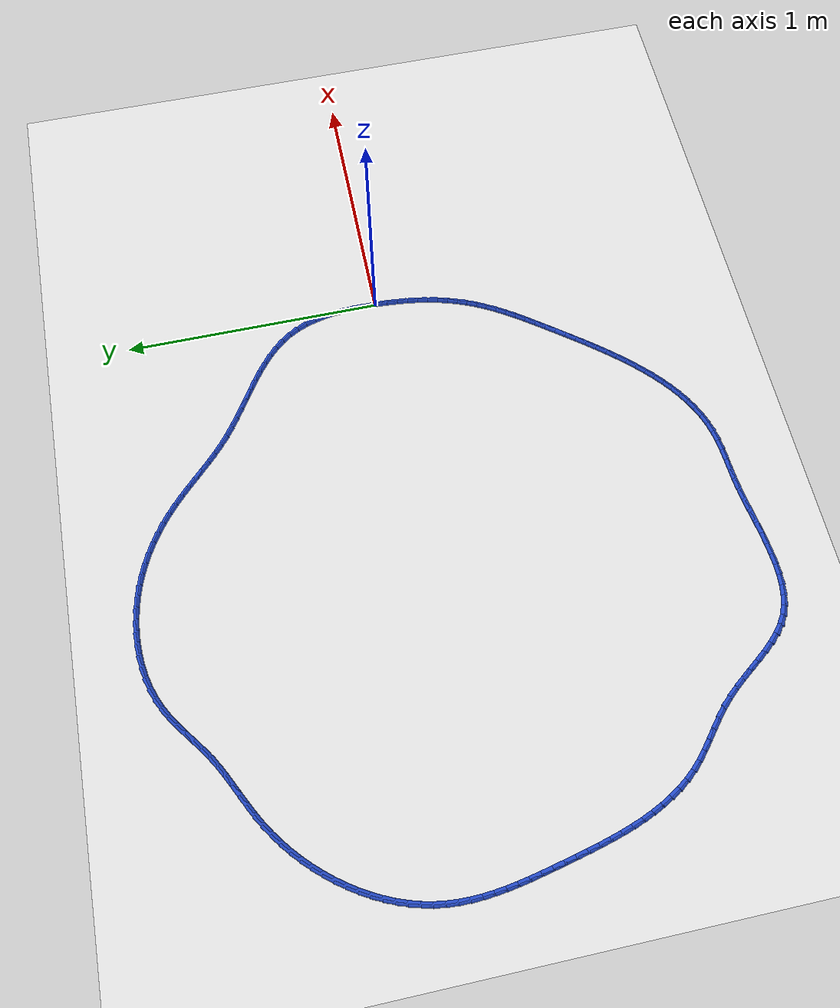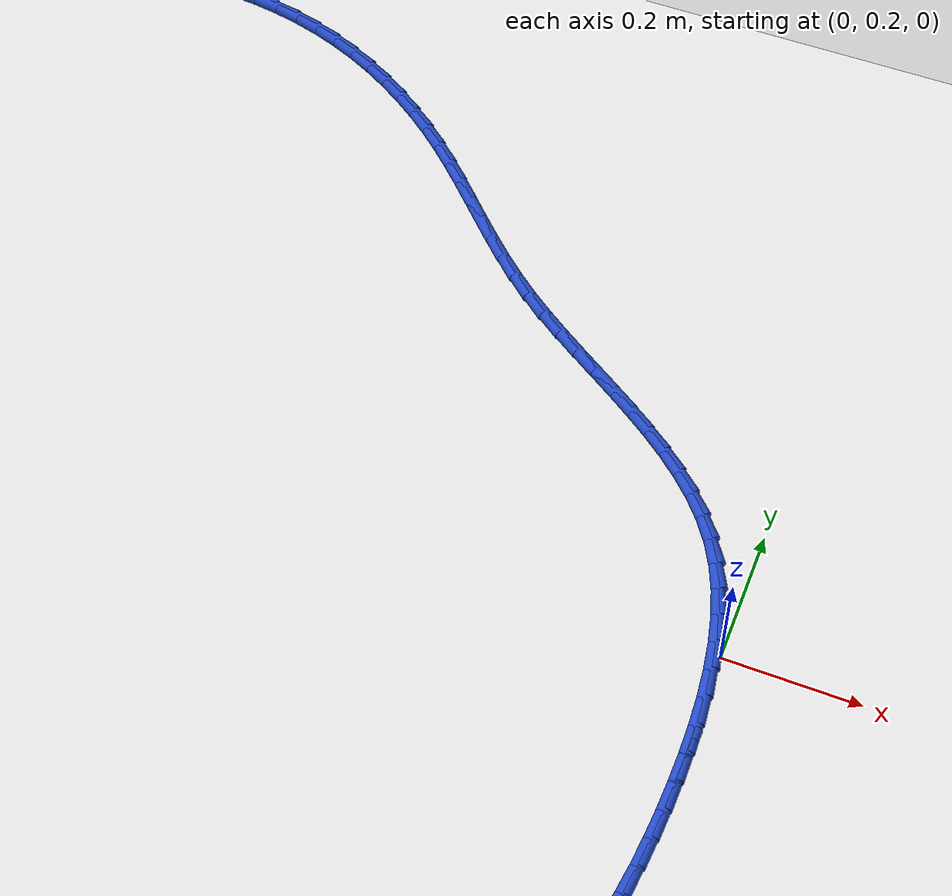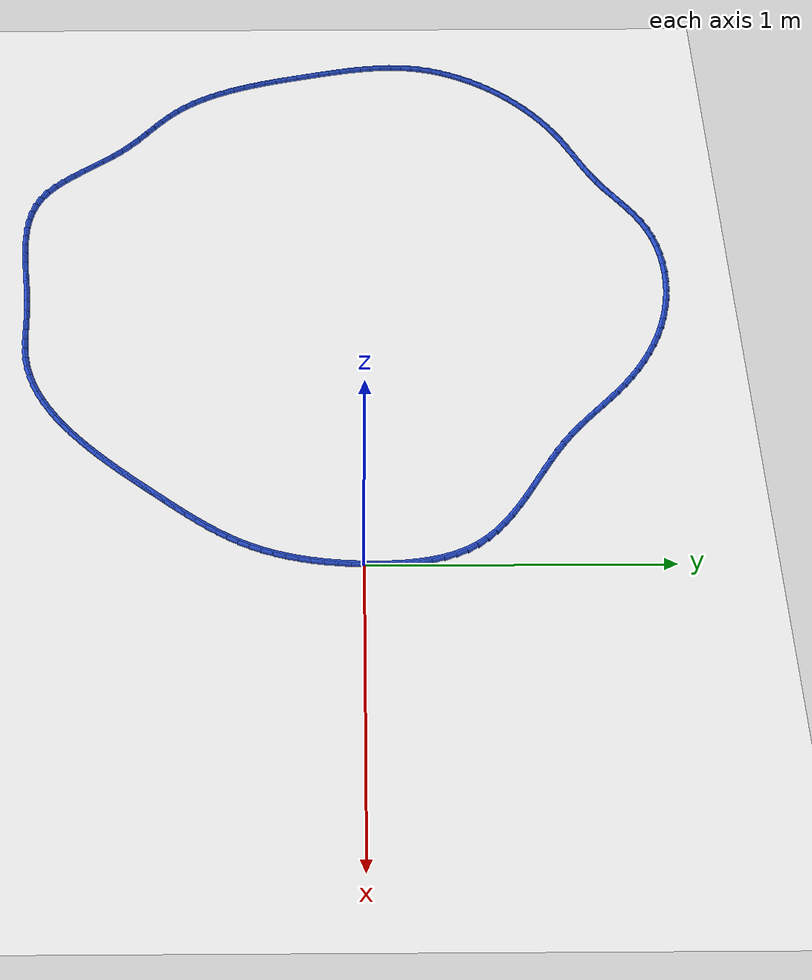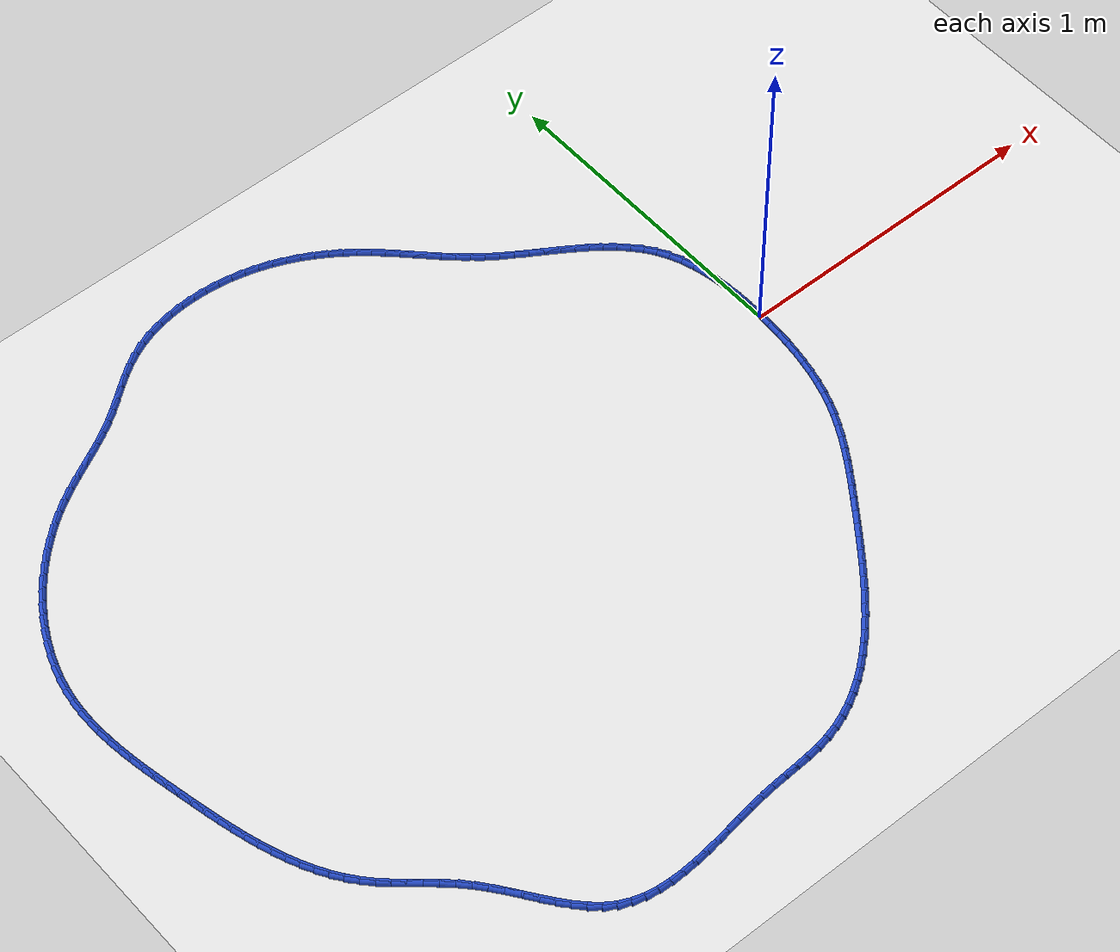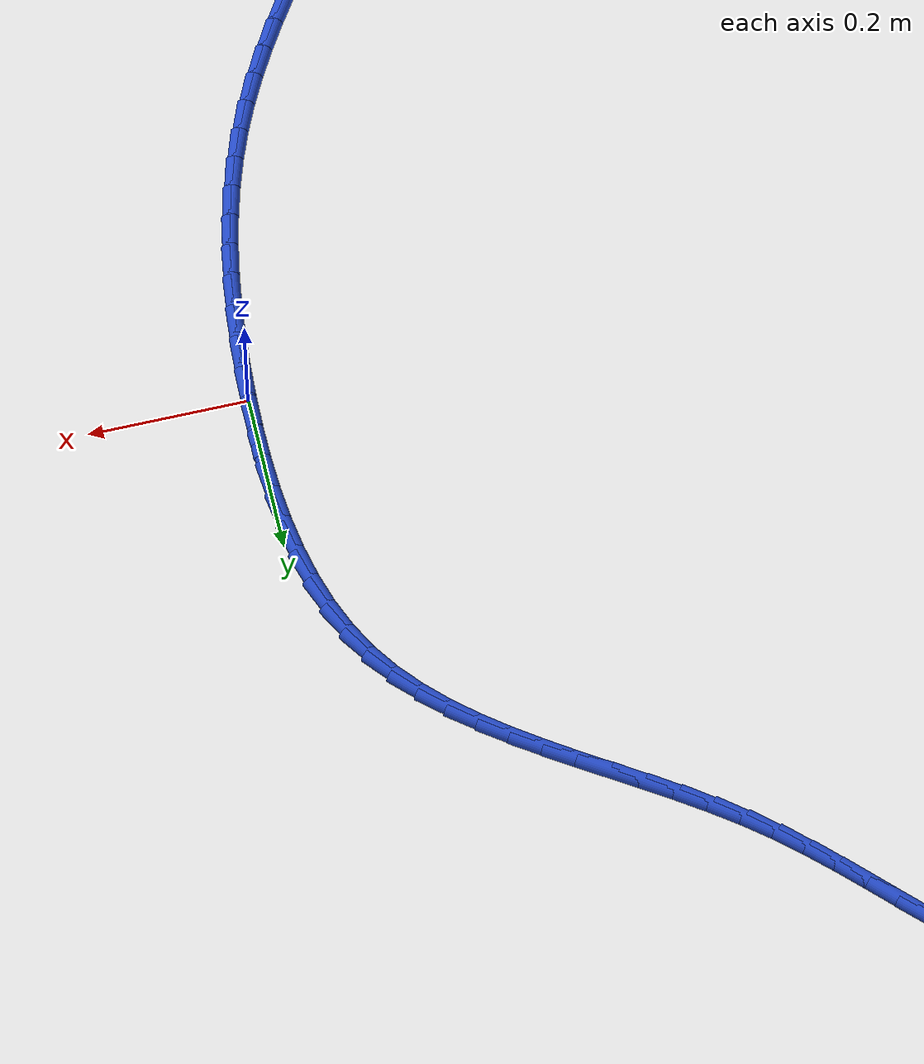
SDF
<sdf version="1.6">
 <world name="default">
  <light name="sun" type="directional">
   <pose>0 0 10 0 -0 0</pose>
   <diffuse>0.8 0.8 0.8 1</diffuse>
   <specular>0.2 0.2 0.2 1</specular>
   <attenuation>
    <range>1000</range>
    <constant>0.9</constant>
    <linear>0.01</linear>
    <quadratic>0.001</quadratic>
   </attenuation>
   <direction>-0.5 0.1 -0.9</direction>
  </light>
  <model name="ground_plane">
   <static>1</static>
   <link name="link">
    <collision name="collision">
     <geometry><plane><normal>0 0 1</normal><size>100 100</size></plane></geometry>
     <surface><friction><ode><mu>100</mu><mu2>50</mu2></ode></friction></surface>
    </collision>
    <visual name="visual">
     <cast_shadows>0</cast_shadows>
     <geometry><plane><normal>0 0 1</normal><size>100 100</size></plane></geometry>
     <material>
      <script><uri>file://media/materials/scripts/gazebo.material</uri><name>Gazebo/WhiteGlow</name></script>
     </material>
    </visual>
   </link>
  </model>
  <gravity>0 0 -9.8</gravity>
  <magnetic_field>6e-06 2.3e-05 -4.2e-05</magnetic_field>
  <atmosphere type="adiabatic"/>
  <physics name="default_physics" default="0" type="ode">
   <max_step_size>0.001</max_step_size>
   <real_time_factor>1</real_time_factor>
   <real_time_update_rate>1000</real_time_update_rate>
  </physics>
  <scene><ambient>0.4 0.4 0.4 1</ambient><background>0.7 0.7 0.7 1</background><shadows>1</shadows></scene>
  <spherical_coordinates>
   <surface_model>EARTH_WGS84</surface_model>
   <latitude_deg>0</latitude_deg>
   <longitude_deg>0</longitude_deg>
   <elevation>0</elevation>
   <heading_deg>0</heading_deg>
  </spherical_coordinates>
  <model name="line">
   <link name="link_0">
    <pose>1.6046192152785466e-17 8.326672684688674e-17 0.01 0 1.57 1.5554259373008228</pose>
    <collision name="collision">
     <geometry><cylinder><radius>0.01</radius><length>0.08</length></cylinder></geometry>
    </collision>
    <visual name="visual">
     <material>
      <script><name>Gazebo/Blue</name><uri>file://media/materials/scripts/gazebo.material</uri></script>
     </material>
     <geometry><cylinder><radius>0.01</radius><length>0.08</length></cylinder></geometry>
    </visual>
   </link>
   <link name="link_1">
    <pose>0.0006633091673790335 0.04315160207646187 0.01 0 1.57 -1.5537687806283904</pose>
    <collision name="collision">
     <geometry><cylinder><radius>0.01</radius><length>0.08</length></cylinder></geometry>
    </collision>
    <visual name="visual">
     <material>
      <script><name>Gazebo/Blue</name><uri>file://media/materials/scripts/gazebo.material</uri></script>
     </material>
     <geometry><cylinder><radius>0.01</radius><length>0.08</length></cylinder></geometry>
    </visual>
   </link>
   <link name="link_2">
    <pose>-7.289730888802675e-05 0.08638362837355847 0.01 0 1.57 -1.5144177519370408</pose>
    <collision name="collision">
     <geometry><cylinder><radius>0.01</radius><length>0.08</length></cylinder></geometry>
    </collision>
    <visual name="visual">
     <material>
      <script><name>Gazebo/Blue</name><uri>file://media/materials/scripts/gazebo.material</uri></script>
     </material>
     <geometry><cylinder><radius>0.01</radius><length>0.08</length></cylinder></geometry>
    </visual>
   </link>
   <link name="link_3">
    <pose>-0.002498578812207435 0.12936291473853773 0.01 0 1.57 -1.4672574481096157</pose>
    <collision name="collision">
     <geometry><cylinder><radius>0.01</radius><length>0.08</length></cylinder></geometry>
    </collision>
    <visual name="visual">
     <material>
      <script><name>Gazebo/Blue</name><uri>file://media/materials/scripts/gazebo.material</uri></script>
     </material>
     <geometry><cylinder><radius>0.01</radius><length>0.08</length></cylinder></geometry>
    </visual>
   </link>
   <link name="link_4">
    <pose>-0.006903694725985474 0.17175629701864756 0.01 0 1.57 -1.4112332738049453</pose>
    <collision name="collision">
     <geometry><cylinder><radius>0.01</radius><length>0.08</length></cylinder></geometry>
    </collision>
    <visual name="visual">
     <material>
      <script><name>Gazebo/Blue</name><uri>file://media/materials/scripts/gazebo.material</uri></script>
     </material>
     <geometry><cylinder><radius>0.01</radius><length>0.08</length></cylinder></geometry>
    </visual>
   </link>
   <link name="link_5">
    <pose>-0.013578204433628416 0.21323061106113592 0.01 0 1.57 -1.3451344930665576</pose>
    <collision name="collision">
     <geometry><cylinder><radius>0.01</radius><length>0.08</length></cylinder></geometry>
    </collision>
    <visual name="visual">
     <material>
      <script><name>Gazebo/Blue</name><uri>file://media/materials/scripts/gazebo.material</uri></script>
     </material>
     <geometry><cylinder><radius>0.01</radius><length>0.08</length></cylinder></geometry>
    </visual>
   </link>
   <link name="link_6">
    <pose>-0.022812067318542538 0.25345269271325055 0.01 0 1.57 -1.2676942745625357</pose>
    <collision name="collision">
     <geometry><cylinder><radius>0.01</radius><length>0.08</length></cylinder></geometry>
    </collision>
    <visual name="visual">
     <material>
      <script><name>Gazebo/Blue</name><uri>file://media/materials/scripts/gazebo.material</uri></script>
     </material>
     <geometry><cylinder><radius>0.01</radius><length>0.08</length></cylinder></geometry>
    </visual>
   </link>
   <link name="link_7">
    <pose>-0.03489524276413412 0.2920893778222395 0.01 0 1.57 -1.1777880586712044</pose>
    <collision name="collision">
     <geometry><cylinder><radius>0.01</radius><length>0.08</length></cylinder></geometry>
    </collision>
    <visual name="visual">
     <material>
      <script><name>Gazebo/Blue</name><uri>file://media/materials/scripts/gazebo.material</uri></script>
     </material>
     <geometry><cylinder><radius>0.01</radius><length>0.08</length></cylinder></geometry>
    </visual>
   </link>
   <link name="link_8">
    <pose>-0.05011769015380943 0.3288075022353504 0.01 0 1.57 -1.074769846922253</pose>
    <collision name="collision">
     <geometry><cylinder><radius>0.01</radius><length>0.08</length></cylinder></geometry>
    </collision>
    <visual name="visual">
     <material>
      <script><name>Gazebo/Blue</name><uri>file://media/materials/scripts/gazebo.material</uri></script>
     </material>
     <geometry><cylinder><radius>0.01</radius><length>0.08</length></cylinder></geometry>
    </visual>
   </link>
   <link name="link_9">
    <pose>-0.06876934157704286 0.3632739264172566 0.01 0 1.57 -0.9638605360832847</pose>
    <collision name="collision">
     <geometry><cylinder><radius>0.01</radius><length>0.08</length></cylinder></geometry>
    </collision>
    <visual name="visual">
     <material>
      <script><name>Gazebo/Blue</name><uri>file://media/materials/scripts/gazebo.material</uri></script>
     </material>
     <geometry><cylinder><radius>0.01</radius><length>0.08</length></cylinder></geometry>
    </visual>
   </link>
   <link name="link_10">
    <pose>-0.0909967035301576 0.3952848717779928 0.01 0 1.57 -0.8632682270970617</pose>
    <collision name="collision">
     <geometry><cylinder><radius>0.01</radius><length>0.08</length></cylinder></geometry>
    </collision>
    <visual name="visual">
     <material>
      <script><name>Gazebo/Blue</name><uri>file://media/materials/scripts/gazebo.material</uri></script>
     </material>
     <geometry><cylinder><radius>0.01</radius><length>0.08</length></cylinder></geometry>
    </visual>
   </link>
   <link name="link_11">
    <pose>-0.11646820613937421 0.42506775481511244 0.01 0 1.57 -0.7780507097465544</pose>
    <collision name="collision">
     <geometry><cylinder><radius>0.01</radius><length>0.08</length></cylinder></geometry>
    </collision>
    <visual name="visual">
     <material>
      <script><name>Gazebo/Blue</name><uri>file://media/materials/scripts/gazebo.material</uri></script>
     </material>
     <geometry><cylinder><radius>0.01</radius><length>0.08</length></cylinder></geometry>
    </visual>
   </link>
   <link name="link_12">
    <pose>-0.14475279095310872 0.45293972452226494 0.01 0 1.57 -0.7084860389107985</pose>
    <collision name="collision">
     <geometry><cylinder><radius>0.01</radius><length>0.08</length></cylinder></geometry>
    </collision>
    <visual name="visual">
     <material>
      <script><name>Gazebo/Blue</name><uri>file://media/materials/scripts/gazebo.material</uri></script>
     </material>
     <geometry><cylinder><radius>0.01</radius><length>0.08</length></cylinder></geometry>
    </visual>
   </link>
   <link name="link_13">
    <pose>-0.17541939951977717 0.47921792989309964 0.01 0 1.57 -0.6539819894974859</pose>
    <collision name="collision">
     <geometry><cylinder><radius>0.01</radius><length>0.08</length></cylinder></geometry>
    </collision>
    <visual name="visual">
     <material>
      <script><name>Gazebo/Blue</name><uri>file://media/materials/scripts/gazebo.material</uri></script>
     </material>
     <geometry><cylinder><radius>0.01</radius><length>0.08</length></cylinder></geometry>
    </visual>
   </link>
   <link name="link_14">
    <pose>-0.20803697338779537 0.5042195199212656 0.01 0 1.57 -0.6135883434165922</pose>
    <collision name="collision">
     <geometry><cylinder><radius>0.01</radius><length>0.08</length></cylinder></geometry>
    </collision>
    <visual name="visual">
     <material>
      <script><name>Gazebo/Blue</name><uri>file://media/materials/scripts/gazebo.material</uri></script>
     </material>
     <geometry><cylinder><radius>0.01</radius><length>0.08</length></cylinder></geometry>
    </visual>
   </link>
   <link name="link_15">
    <pose>-0.24217445410557945 0.5282616436004123 0.01 0 1.57 -0.5863417867000147</pose>
    <collision name="collision">
     <geometry><cylinder><radius>0.01</radius><length>0.08</length></cylinder></geometry>
    </collision>
    <visual name="visual">
     <material>
      <script><name>Gazebo/Blue</name><uri>file://media/materials/scripts/gazebo.material</uri></script>
     </material>
     <geometry><cylinder><radius>0.01</radius><length>0.08</length></cylinder></geometry>
    </visual>
   </link>
   <link name="link_16">
    <pose>-0.2774007832215454 0.5516614499241891 0.01 0 1.57 -0.5714612175682233</pose>
    <collision name="collision">
     <geometry><cylinder><radius>0.01</radius><length>0.08</length></cylinder></geometry>
    </collision>
    <visual name="visual">
     <material>
      <script><name>Gazebo/Blue</name><uri>file://media/materials/scripts/gazebo.material</uri></script>
     </material>
     <geometry><cylinder><radius>0.01</radius><length>0.08</length></cylinder></geometry>
    </visual>
   </link>
   <link name="link_17">
    <pose>-0.31328490228410927 0.5747360878862453 0.01 0 1.57 -0.5684418973338173</pose>
    <collision name="collision">
     <geometry><cylinder><radius>0.01</radius><length>0.08</length></cylinder></geometry>
    </collision>
    <visual name="visual">
     <material>
      <script><name>Gazebo/Blue</name><uri>file://media/materials/scripts/gazebo.material</uri></script>
     </material>
     <geometry><cylinder><radius>0.01</radius><length>0.08</length></cylinder></geometry>
    </visual>
   </link>
   <link name="link_18">
    <pose>-0.3493957528416869 0.59780270648023 0.01 0 1.57 -0.5770896497452037</pose>
    <collision name="collision">
     <geometry><cylinder><radius>0.01</radius><length>0.08</length></cylinder></geometry>
    </collision>
    <visual name="visual">
     <material>
      <script><name>Gazebo/Blue</name><uri>file://media/materials/scripts/gazebo.material</uri></script>
     </material>
     <geometry><cylinder><radius>0.01</radius><length>0.08</length></cylinder></geometry>
    </visual>
   </link>
   <link name="link_19">
    <pose>-0.3853022764426942 0.6211784546997925 0.01 0 1.57 -0.5975188175409447</pose>
    <collision name="collision">
     <geometry><cylinder><radius>0.01</radius><length>0.08</length></cylinder></geometry>
    </collision>
    <visual name="visual">
     <material>
      <script><name>Gazebo/Blue</name><uri>file://media/materials/scripts/gazebo.material</uri></script>
     </material>
     <geometry><cylinder><radius>0.01</radius><length>0.08</length></cylinder></geometry>
    </visual>
   </link>
   <link name="link_20">
    <pose>-0.42057341463554765 0.6451804815385827 0.01 0 1.57 -0.6301203983193765</pose>
    <collision name="collision">
     <geometry><cylinder><radius>0.01</radius><length>0.08</length></cylinder></geometry>
    </collision>
    <visual name="visual">
     <material>
      <script><name>Gazebo/Blue</name><uri>file://media/materials/scripts/gazebo.material</uri></script>
     </material>
     <geometry><cylinder><radius>0.01</radius><length>0.08</length></cylinder></geometry>
    </visual>
   </link>
   <link name="link_21">
    <pose>-0.45477810896866283 0.6701259359902492 0.01 0 1.57 -0.6751307637914237</pose>
    <collision name="collision">
     <geometry><cylinder><radius>0.01</radius><length>0.08</length></cylinder></geometry>
    </collision>
    <visual name="visual">
     <material>
      <script><name>Gazebo/Blue</name><uri>file://media/materials/scripts/gazebo.material</uri></script>
     </material>
     <geometry><cylinder><radius>0.01</radius><length>0.08</length></cylinder></geometry>
    </visual>
   </link>
   <link name="link_22">
    <pose>-0.4874972822513894 0.6963221987514964 0.01 0 1.57 -0.7219948559214293</pose>
    <collision name="collision">
     <geometry><cylinder><radius>0.01</radius><length>0.08</length></cylinder></geometry>
    </collision>
    <visual name="visual">
     <material>
      <script><name>Gazebo/Blue</name><uri>file://media/materials/scripts/gazebo.material</uri></script>
     </material>
     <geometry><cylinder><radius>0.01</radius><length>0.08</length></cylinder></geometry>
    </visual>
   </link>
   <link name="link_23">
    <pose>-0.5186768723717735 0.7237790544898816 0.01 0 1.57 -0.7575506675270957</pose>
    <collision name="collision">
     <geometry><cylinder><radius>0.01</radius><length>0.08</length></cylinder></geometry>
    </collision>
    <visual name="visual">
     <material>
      <script><name>Gazebo/Blue</name><uri>file://media/materials/scripts/gazebo.material</uri></script>
     </material>
     <geometry><cylinder><radius>0.01</radius><length>0.08</length></cylinder></geometry>
    </visual>
   </link>
   <link name="link_24">
    <pose>-0.5486857562644942 0.7521614665540748 0.01 0 1.57 -0.7806366892263387</pose>
    <collision name="collision">
     <geometry><cylinder><radius>0.01</radius><length>0.08</length></cylinder></geometry>
    </collision>
    <visual name="visual">
     <material>
      <script><name>Gazebo/Blue</name><uri>file://media/materials/scripts/gazebo.material</uri></script>
     </material>
     <geometry><cylinder><radius>0.01</radius><length>0.08</length></cylinder></geometry>
    </visual>
   </link>
   <link name="link_25">
    <pose>-0.5779164557598304 0.7811151206588872 0.01 0 1.57 -0.7910094370864703</pose>
    <collision name="collision">
     <geometry><cylinder><radius>0.01</radius><length>0.08</length></cylinder></geometry>
    </collision>
    <visual name="visual">
     <material>
      <script><name>Gazebo/Blue</name><uri>file://media/materials/scripts/gazebo.material</uri></script>
     </material>
     <geometry><cylinder><radius>0.01</radius><length>0.08</length></cylinder></geometry>
    </visual>
   </link>
   <link name="link_26">
    <pose>-0.606761492688061 0.8102857025191302 0.01 0 1.57 -0.7885302055430883</pose>
    <collision name="collision">
     <geometry><cylinder><radius>0.01</radius><length>0.08</length></cylinder></geometry>
    </collision>
    <visual name="visual">
     <material>
      <script><name>Gazebo/Blue</name><uri>file://media/materials/scripts/gazebo.material</uri></script>
     </material>
     <geometry><cylinder><radius>0.01</radius><length>0.08</length></cylinder></geometry>
    </visual>
   </link>
   <link name="link_27">
    <pose>-0.635613388879465 0.8393188978496147 0.01 0 1.57 -0.7731172662609904</pose>
    <collision name="collision">
     <geometry><cylinder><radius>0.01</radius><length>0.08</length></cylinder></geometry>
    </collision>
    <visual name="visual">
     <material>
      <script><name>Gazebo/Blue</name><uri>file://media/materials/scripts/gazebo.material</uri></script>
     </material>
     <geometry><cylinder><radius>0.01</radius><length>0.08</length></cylinder></geometry>
    </visual>
   </link>
   <link name="link_28">
    <pose>-0.6648646661643216 0.8678603923651526 0.01 0 1.57 -0.7447597372337205</pose>
    <collision name="collision">
     <geometry><cylinder><radius>0.01</radius><length>0.08</length></cylinder></geometry>
    </collision>
    <visual name="visual">
     <material>
      <script><name>Gazebo/Blue</name><uri>file://media/materials/scripts/gazebo.material</uri></script>
     </material>
     <geometry><cylinder><radius>0.01</radius><length>0.08</length></cylinder></geometry>
    </visual>
   </link>
   <link name="link_29">
    <pose>-0.6949078463729097 0.8955558717805542 0.01 0 1.57 -0.7042297623080148</pose>
    <collision name="collision">
     <geometry><cylinder><radius>0.01</radius><length>0.08</length></cylinder></geometry>
    </collision>
    <visual name="visual">
     <material>
      <script><name>Gazebo/Blue</name><uri>file://media/materials/scripts/gazebo.material</uri></script>
     </material>
     <geometry><cylinder><radius>0.01</radius><length>0.08</length></cylinder></geometry>
    </visual>
   </link>
   <link name="link_30">
    <pose>-0.7261103180784759 0.9220637706807228 0.01 0 1.57 -0.6579464693569888</pose>
    <collision name="collision">
     <geometry><cylinder><radius>0.01</radius><length>0.08</length></cylinder></geometry>
    </collision>
    <visual name="visual">
     <material>
      <script><name>Gazebo/Blue</name><uri>file://media/materials/scripts/gazebo.material</uri></script>
     </material>
     <geometry><cylinder><radius>0.01</radius><length>0.08</length></cylinder></geometry>
    </visual>
   </link>
   <link name="link_31">
    <pose>-0.758593405297822 0.9471673401461038 0.01 0 1.57 -0.6093549037237832</pose>
    <collision name="collision">
     <geometry><cylinder><radius>0.01</radius><length>0.08</length></cylinder></geometry>
    </collision>
    <visual name="visual">
     <material>
      <script><name>Gazebo/Blue</name><uri>file://media/materials/scripts/gazebo.material</uri></script>
     </material>
     <geometry><cylinder><radius>0.01</radius><length>0.08</length></cylinder></geometry>
    </visual>
   </link>
   <link name="link_32">
    <pose>-0.7923391443933556 0.9707204850609442 0.01 0 1.57 -0.5583814923259558</pose>
    <collision name="collision">
     <geometry><cylinder><radius>0.01</radius><length>0.08</length></cylinder></geometry>
    </collision>
    <visual name="visual">
     <material>
      <script><name>Gazebo/Blue</name><uri>file://media/materials/scripts/gazebo.material</uri></script>
     </material>
     <geometry><cylinder><radius>0.01</radius><length>0.08</length></cylinder></geometry>
    </visual>
   </link>
   <link name="link_33">
    <pose>-0.8273279865640331 0.992577914385258 0.01 0 1.57 -0.5049525181580293</pose>
    <collision name="collision">
     <geometry><cylinder><radius>0.01</radius><length>0.08</length></cylinder></geometry>
    </collision>
    <visual name="visual">
     <material>
      <script><name>Gazebo/Blue</name><uri>file://media/materials/scripts/gazebo.material</uri></script>
     </material>
     <geometry><cylinder><radius>0.01</radius><length>0.08</length></cylinder></geometry>
    </visual>
   </link>
   <link name="link_34">
    <pose>-0.8635403830088104 1.0125943370790584 0.01 0 1.57 -0.44904484457241683</pose>
    <collision name="collision">
     <geometry><cylinder><radius>0.01</radius><length>0.08</length></cylinder></geometry>
    </collision>
    <visual name="visual">
     <material>
      <script><name>Gazebo/Blue</name><uri>file://media/materials/scripts/gazebo.material</uri></script>
     </material>
     <geometry><cylinder><radius>0.01</radius><length>0.08</length></cylinder></geometry>
    </visual>
   </link>
   <link name="link_35">
    <pose>-0.9009567849266448 1.0306244621023593 0.01 0 1.57 -0.39069708512705065</pose>
    <collision name="collision">
     <geometry><cylinder><radius>0.01</radius><length>0.08</length></cylinder></geometry>
    </collision>
    <visual name="visual">
     <material>
      <script><name>Gazebo/Blue</name><uri>file://media/materials/scripts/gazebo.material</uri></script>
     </material>
     <geometry><cylinder><radius>0.01</radius><length>0.08</length></cylinder></geometry>
    </visual>
   </link>
   <link name="link_36">
    <pose>-0.9395576435164927 1.0465229984151745 0.01 0 1.57 -0.3300200909865129</pose>
    <collision name="collision">
     <geometry><cylinder><radius>0.01</radius><length>0.08</length></cylinder></geometry>
    </collision>
    <visual name="visual">
     <material>
      <script><name>Gazebo/Blue</name><uri>file://media/materials/scripts/gazebo.material</uri></script>
     </material>
     <geometry><cylinder><radius>0.01</radius><length>0.08</length></cylinder></geometry>
    </visual>
   </link>
   <link name="link_37">
    <pose>-0.9793234099773103 1.0601446549775173 0.01 0 1.57 -0.26771507477092094</pose>
    <collision name="collision">
     <geometry><cylinder><radius>0.01</radius><length>0.08</length></cylinder></geometry>
    </collision>
    <visual name="visual">
     <material>
      <script><name>Gazebo/Blue</name><uri>file://media/materials/scripts/gazebo.material</uri></script>
     </material>
     <geometry><cylinder><radius>0.01</radius><length>0.08</length></cylinder></geometry>
    </visual>
   </link>
   <link name="link_38">
    <pose>-1.020191773545227 1.0713548367638819 0.01 0 1.57 -0.20565964276784215</pose>
    <collision name="collision">
     <geometry><cylinder><radius>0.01</radius><length>0.08</length></cylinder></geometry>
    </collision>
    <visual name="visual">
     <material>
      <script><name>Gazebo/Blue</name><uri>file://media/materials/scripts/gazebo.material</uri></script>
     </material>
     <geometry><cylinder><radius>0.01</radius><length>0.08</length></cylinder></geometry>
    </visual>
   </link>
   <link name="link_39">
    <pose>-1.0619294925193994 1.0800617035629956 0.01 0 1.57 -0.14363498870059255</pose>
    <collision name="collision">
     <geometry><cylinder><radius>0.01</radius><length>0.08</length></cylinder></geometry>
    </collision>
    <visual name="visual">
     <material>
      <script><name>Gazebo/Blue</name><uri>file://media/materials/scripts/gazebo.material</uri></script>
     </material>
     <geometry><cylinder><radius>0.01</radius><length>0.08</length></cylinder></geometry>
    </visual>
   </link>
   <link name="link_40">
    <pose>-1.1042606216733475 1.0861840965612197 0.01 0 1.57 -0.08087536014928524</pose>
    <collision name="collision">
     <geometry><cylinder><radius>0.01</radius><length>0.08</length></cylinder></geometry>
    </collision>
    <visual name="visual">
     <material>
      <script><name>Gazebo/Blue</name><uri>file://media/materials/scripts/gazebo.material</uri></script>
     </material>
     <geometry><cylinder><radius>0.01</radius><length>0.08</length></cylinder></geometry>
    </visual>
   </link>
   <link name="link_41">
    <pose>-1.1469092157805925 1.089640856944916 0.01 0 1.57 -0.016629225076414005</pose>
    <collision name="collision">
     <geometry><cylinder><radius>0.01</radius><length>0.08</length></cylinder></geometry>
    </collision>
    <visual name="visual">
     <material>
      <script><name>Gazebo/Blue</name><uri>file://media/materials/scripts/gazebo.material</uri></script>
     </material>
     <geometry><cylinder><radius>0.01</radius><length>0.08</length></cylinder></geometry>
    </visual>
   </link>
   <link name="link_42">
    <pose>-1.1895993296146534 1.0903508259004453 0.01 0 1.57 0.049845544423002396</pose>
    <collision name="collision">
     <geometry><cylinder><radius>0.01</radius><length>0.08</length></cylinder></geometry>
    </collision>
    <visual name="visual">
     <material>
      <script><name>Gazebo/Blue</name><uri>file://media/materials/scripts/gazebo.material</uri></script>
     </material>
     <geometry><cylinder><radius>0.01</radius><length>0.08</length></cylinder></geometry>
    </visual>
   </link>
   <link name="link_43">
    <pose>-1.2320550179490515 1.0882328446141687 0.01 0 1.57 0.1192797371865166</pose>
    <collision name="collision">
     <geometry><cylinder><radius>0.01</radius><length>0.08</length></cylinder></geometry>
    </collision>
    <visual name="visual">
     <material>
      <script><name>Gazebo/Blue</name><uri>file://media/materials/scripts/gazebo.material</uri></script>
     </material>
     <geometry><cylinder><radius>0.01</radius><length>0.08</length></cylinder></geometry>
    </visual>
   </link>
   <link name="link_44">
    <pose>-1.2740003355573066 1.0832057542724478 0.01 0 1.57 0.192380875098213</pose>
    <collision name="collision">
     <geometry><cylinder><radius>0.01</radius><length>0.08</length></cylinder></geometry>
    </collision>
    <visual name="visual">
     <material>
      <script><name>Gazebo/Blue</name><uri>file://media/materials/scripts/gazebo.material</uri></script>
     </material>
     <geometry><cylinder><radius>0.01</radius><length>0.08</length></cylinder></geometry>
    </visual>
   </link>
   <link name="link_45">
    <pose>-1.3151593372129404 1.075188396061644 0.01 0 1.57 0.26980738724072</pose>
    <collision name="collision">
     <geometry><cylinder><radius>0.01</radius><length>0.08</length></cylinder></geometry>
    </collision>
    <visual name="visual">
     <material>
      <script><name>Gazebo/Blue</name><uri>file://media/materials/scripts/gazebo.material</uri></script>
     </material>
     <geometry><cylinder><radius>0.01</radius><length>0.08</length></cylinder></geometry>
    </visual>
   </link>
   <link name="link_46">
    <pose>-1.3552560776894713 1.0640996111681182 0.01 0 1.57 0.35212482222239866</pose>
    <collision name="collision">
     <geometry><cylinder><radius>0.01</radius><length>0.08</length></cylinder></geometry>
    </collision>
    <visual name="visual">
     <material>
      <script><name>Gazebo/Blue</name><uri>file://media/materials/scripts/gazebo.material</uri></script>
     </material>
     <geometry><cylinder><radius>0.01</radius><length>0.08</length></cylinder></geometry>
    </visual>
   </link>
   <link name="link_47">
    <pose>-1.3940146117604215 1.0498582407782322 0.01 0 1.57 0.4397413068819108</pose>
    <collision name="collision">
     <geometry><cylinder><radius>0.01</radius><length>0.08</length></cylinder></geometry>
    </collision>
    <visual name="visual">
     <material>
      <script><name>Gazebo/Blue</name><uri>file://media/materials/scripts/gazebo.material</uri></script>
     </material>
     <geometry><cylinder><radius>0.01</radius><length>0.08</length></cylinder></geometry>
    </visual>
   </link>
   <link name="link_48">
    <pose>-1.4311589941993095 1.0323831260783467 0.01 0 1.57 0.529278528474185</pose>
    <collision name="collision">
     <geometry><cylinder><radius>0.01</radius><length>0.08</length></cylinder></geometry>
    </collision>
    <visual name="visual">
     <material>
      <script><name>Gazebo/Blue</name><uri>file://media/materials/scripts/gazebo.material</uri></script>
     </material>
     <geometry><cylinder><radius>0.01</radius><length>0.08</length></cylinder></geometry>
    </visual>
   </link>
   <link name="link_49">
    <pose>-1.4665048682250175 1.0117076182102842 0.01 0 1.57 0.6000278033007083</pose>
    <collision name="collision">
     <geometry><cylinder><radius>0.01</radius><length>0.08</length></cylinder></geometry>
    </collision>
    <visual name="visual">
     <material>
      <script><name>Gazebo/Blue</name><uri>file://media/materials/scripts/gazebo.material</uri></script>
     </material>
     <geometry><cylinder><radius>0.01</radius><length>0.08</length></cylinder></geometry>
    </visual>
   </link>
   <link name="link_50">
    <pose>-1.5003932609493436 0.9885219381419786 0.01 0 1.57 0.6445224519959704</pose>
    <collision name="collision">
     <geometry><cylinder><radius>0.01</radius><length>0.08</length></cylinder></geometry>
    </collision>
    <visual name="visual">
     <material>
      <script><name>Gazebo/Blue</name><uri>file://media/materials/scripts/gazebo.material</uri></script>
     </material>
     <geometry><cylinder><radius>0.01</radius><length>0.08</length></cylinder></geometry>
    </visual>
   </link>
   <link name="link_51">
    <pose>-1.5333521943705068 0.9637501002640098 0.01 0 1.57 0.6631643925983046</pose>
    <collision name="collision">
     <geometry><cylinder><radius>0.01</radius><length>0.08</length></cylinder></geometry>
    </collision>
    <visual name="visual">
     <material>
      <script><name>Gazebo/Blue</name><uri>file://media/materials/scripts/gazebo.material</uri></script>
     </material>
     <geometry><cylinder><radius>0.01</radius><length>0.08</length></cylinder></geometry>
    </visual>
   </link>
   <link name="link_52">
    <pose>-1.5659099174969364 0.9383164027901909 0.01 0 1.57 0.6562553935677533</pose>
    <collision name="collision">
     <geometry><cylinder><radius>0.01</radius><length>0.08</length></cylinder></geometry>
    </collision>
    <visual name="visual">
     <material>
      <script><name>Gazebo/Blue</name><uri>file://media/materials/scripts/gazebo.material</uri></script>
     </material>
     <geometry><cylinder><radius>0.01</radius><length>0.08</length></cylinder></geometry>
    </visual>
   </link>
   <link name="link_53">
    <pose>-1.5985946793370591 0.9131451439343354 0.01 0 1.57 0.6236216678948734</pose>
    <collision name="collision">
     <geometry><cylinder><radius>0.01</radius><length>0.08</length></cylinder></geometry>
    </collision>
    <visual name="visual">
     <material>
      <script><name>Gazebo/Blue</name><uri>file://media/materials/scripts/gazebo.material</uri></script>
     </material>
     <geometry><cylinder><radius>0.01</radius><length>0.08</length></cylinder></geometry>
    </visual>
   </link>
   <link name="link_54">
    <pose>-1.631934728899303 0.8891606219102567 0.01 0 1.57 0.5705331269557472</pose>
    <collision name="collision">
     <geometry><cylinder><radius>0.01</radius><length>0.08</length></cylinder></geometry>
    </collision>
    <visual name="visual">
     <material>
      <script><name>Gazebo/Blue</name><uri>file://media/materials/scripts/gazebo.material</uri></script>
     </material>
     <geometry><cylinder><radius>0.01</radius><length>0.08</length></cylinder></geometry>
    </visual>
   </link>
   <link name="link_55">
    <pose>-1.6663455886523997 0.8670784517453487 0.01 0 1.57 0.5250505709806931</pose>
    <collision name="collision">
     <geometry><cylinder><radius>0.01</radius><length>0.08</length></cylinder></geometry>
    </collision>
    <visual name="visual">
     <material>
      <script><name>Gazebo/Blue</name><uri>file://media/materials/scripts/gazebo.material</uri></script>
     </material>
     <geometry><cylinder><radius>0.01</radius><length>0.08</length></cylinder></geometry>
    </visual>
   </link>
   <link name="link_56">
    <pose>-1.7016953282033824 0.8466007851964921 0.01 0 1.57 0.49606289201374787</pose>
    <collision name="collision">
     <geometry><cylinder><radius>0.01</radius><length>0.08</length></cylinder></geometry>
    </collision>
    <visual name="visual">
     <material>
      <script><name>Gazebo/Blue</name><uri>file://media/materials/scripts/gazebo.material</uri></script>
     </material>
     <geometry><cylinder><radius>0.01</radius><length>0.08</length></cylinder></geometry>
    </visual>
   </link>
   <link name="link_57">
    <pose>-1.737686062270652 0.8271225527126526 0.01 0 1.57 0.4836344355855861</pose>
    <collision name="collision">
     <geometry><cylinder><radius>0.01</radius><length>0.08</length></cylinder></geometry>
    </collision>
    <visual name="visual">
     <material>
      <script><name>Gazebo/Blue</name><uri>file://media/materials/scripts/gazebo.material</uri></script>
     </material>
     <geometry><cylinder><radius>0.01</radius><length>0.08</length></cylinder></geometry>
    </visual>
   </link>
   <link name="link_58">
    <pose>-1.7740198685943398 0.8080386162873745 0.01 0 1.57 0.48765750594170243</pose>
    <collision name="collision">
     <geometry><cylinder><radius>0.01</radius><length>0.08</length></cylinder></geometry>
    </collision>
    <visual name="visual">
     <material>
      <script><name>Gazebo/Blue</name><uri>file://media/materials/scripts/gazebo.material</uri></script>
     </material>
     <geometry><cylinder><radius>0.01</radius><length>0.08</length></cylinder></geometry>
    </visual>
   </link>
   <link name="link_59">
    <pose>-1.810398824914579 0.7887438379142044 0.01 0 1.57 0.5079580619278099</pose>
    <collision name="collision">
     <geometry><cylinder><radius>0.01</radius><length>0.08</length></cylinder></geometry>
    </collision>
    <visual name="visual">
     <material>
      <script><name>Gazebo/Blue</name><uri>file://media/materials/scripts/gazebo.material</uri></script>
     </material>
     <geometry><cylinder><radius>0.01</radius><length>0.08</length></cylinder></geometry>
    </visual>
   </link>
   <link name="link_60">
    <pose>-1.8465250089715013 0.7686330795866873 0.01 0 1.57 0.5442669717111053</pose>
    <collision name="collision">
     <geometry><cylinder><radius>0.01</radius><length>0.08</length></cylinder></geometry>
    </collision>
    <visual name="visual">
     <material>
      <script><name>Gazebo/Blue</name><uri>file://media/materials/scripts/gazebo.material</uri></script>
     </material>
     <geometry><cylinder><radius>0.01</radius><length>0.08</length></cylinder></geometry>
    </visual>
   </link>
   <link name="link_61">
    <pose>-1.8821004985052403 0.7471012032983684 0.01 0 1.57 0.5942408515598054</pose>
    <collision name="collision">
     <geometry><cylinder><radius>0.01</radius><length>0.08</length></cylinder></geometry>
    </collision>
    <visual name="visual">
     <material>
      <script><name>Gazebo/Blue</name><uri>file://media/materials/scripts/gazebo.material</uri></script>
     </material>
     <geometry><cylinder><radius>0.01</radius><length>0.08</length></cylinder></geometry>
    </visual>
   </link>
   <link name="link_62">
    <pose>-1.9168458789549185 0.723623220968672 0.01 0 1.57 0.6465886437620075</pose>
    <collision name="collision">
     <geometry><cylinder><radius>0.01</radius><length>0.08</length></cylinder></geometry>
    </collision>
    <visual name="visual">
     <material>
      <script><name>Gazebo/Blue</name><uri>file://media/materials/scripts/gazebo.material</uri></script>
     </material>
     <geometry><cylinder><radius>0.01</radius><length>0.08</length></cylinder></geometry>
    </visual>
   </link>
   <link name="link_63">
    <pose>-1.9505917627675937 0.6981506303586363 0.01 0 1.57 0.6976095394698779</pose>
    <collision name="collision">
     <geometry><cylinder><radius>0.01</radius><length>0.08</length></cylinder></geometry>
    </collision>
    <visual name="visual">
     <material>
      <script><name>Gazebo/Blue</name><uri>file://media/materials/scripts/gazebo.material</uri></script>
     </material>
     <geometry><cylinder><radius>0.01</radius><length>0.08</length></cylinder></geometry>
    </visual>
   </link>
   <link name="link_64">
    <pose>-1.983209260358998 0.6708103107928938 0.01 0 1.57 0.7477035155843117</pose>
    <collision name="collision">
     <geometry><cylinder><radius>0.01</radius><length>0.08</length></cylinder></geometry>
    </collision>
    <visual name="visual">
     <material>
      <script><name>Gazebo/Blue</name><uri>file://media/materials/scripts/gazebo.material</uri></script>
     </material>
     <geometry><cylinder><radius>0.01</radius><length>0.08</length></cylinder></geometry>
    </visual>
   </link>
   <link name="link_65">
    <pose>-2.014569545200757 0.6417294146675757 0.01 0 1.57 0.7972665981418684</pose>
    <collision name="collision">
     <geometry><cylinder><radius>0.01</radius><length>0.08</length></cylinder></geometry>
    </collision>
    <visual name="visual">
     <material>
      <script><name>Gazebo/Blue</name><uri>file://media/materials/scripts/gazebo.material</uri></script>
     </material>
     <geometry><cylinder><radius>0.01</radius><length>0.08</length></cylinder></geometry>
    </visual>
   </link>
   <link name="link_66">
    <pose>-2.0445437907644965 0.6110350943788135 0.01 0 1.57 0.8466869745176493</pose>
    <collision name="collision">
     <geometry><cylinder><radius>0.01</radius><length>0.08</length></cylinder></geometry>
    </collision>
    <visual name="visual">
     <material>
      <script><name>Gazebo/Blue</name><uri>file://media/materials/scripts/gazebo.material</uri></script>
     </material>
     <geometry><cylinder><radius>0.01</radius><length>0.08</length></cylinder></geometry>
    </visual>
   </link>
   <link name="link_67">
    <pose>-2.073003170521842 0.5788545023227392 0.01 0 1.57 0.8963478206045298</pose>
    <collision name="collision">
     <geometry><cylinder><radius>0.01</radius><length>0.08</length></cylinder></geometry>
    </collision>
    <visual name="visual">
     <material>
      <script><name>Gazebo/Blue</name><uri>file://media/materials/scripts/gazebo.material</uri></script>
     </material>
     <geometry><cylinder><radius>0.01</radius><length>0.08</length></cylinder></geometry>
    </visual>
   </link>
   <link name="link_68">
    <pose>-2.0998188579444186 0.5453147908954833 0.01 0 1.57 0.9466300974054627</pose>
    <collision name="collision">
     <geometry><cylinder><radius>0.01</radius><length>0.08</length></cylinder></geometry>
    </collision>
    <visual name="visual">
     <material>
      <script><name>Gazebo/Blue</name><uri>file://media/materials/scripts/gazebo.material</uri></script>
     </material>
     <geometry><cylinder><radius>0.01</radius><length>0.08</length></cylinder></geometry>
    </visual>
   </link>
   <link name="link_69">
    <pose>-2.1248620265038527 0.510543112493178 0.01 0 1.57 0.9979148447080812</pose>
    <collision name="collision">
     <geometry><cylinder><radius>0.01</radius><length>0.08</length></cylinder></geometry>
    </collision>
    <visual name="visual">
     <material>
      <script><name>Gazebo/Blue</name><uri>file://media/materials/scripts/gazebo.material</uri></script>
     </material>
     <geometry><cylinder><radius>0.01</radius><length>0.08</length></cylinder></geometry>
    </visual>
   </link>
   <link name="link_70">
    <pose>-2.148003849671769 0.4746666195119546 0.01 0 1.57 1.0505844690851713</pose>
    <collision name="collision">
     <geometry><cylinder><radius>0.01</radius><length>0.08</length></cylinder></geometry>
    </collision>
    <visual name="visual">
     <material>
      <script><name>Gazebo/Blue</name><uri>file://media/materials/scripts/gazebo.material</uri></script>
     </material>
     <geometry><cylinder><radius>0.01</radius><length>0.08</length></cylinder></geometry>
    </visual>
   </link>
   <link name="link_71">
    <pose>-2.1691155009197938 0.4378124643479443 0.01 0 1.57 1.1050224340860124</pose>
    <collision name="collision">
     <geometry><cylinder><radius>0.01</radius><length>0.08</length></cylinder></geometry>
    </collision>
    <visual name="visual">
     <material>
      <script><name>Gazebo/Blue</name><uri>file://media/materials/scripts/gazebo.material</uri></script>
     </material>
     <geometry><cylinder><radius>0.01</radius><length>0.08</length></cylinder></geometry>
    </visual>
   </link>
   <link name="link_72">
    <pose>-2.1880681537195517 0.40010779939727886 0.01 0 1.57 1.1616106235452164</pose>
    <collision name="collision">
     <geometry><cylinder><radius>0.01</radius><length>0.08</length></cylinder></geometry>
    </collision>
    <visual name="visual">
     <material>
      <script><name>Gazebo/Blue</name><uri>file://media/materials/scripts/gazebo.material</uri></script>
     </material>
     <geometry><cylinder><radius>0.01</radius><length>0.08</length></cylinder></geometry>
    </visual>
   </link>
   <link name="link_73">
    <pose>-2.20473298154267 0.36167977705609 0.01 0 1.57 1.220723487088562</pose>
    <collision name="collision">
     <geometry><cylinder><radius>0.01</radius><length>0.08</length></cylinder></geometry>
    </collision>
    <visual name="visual">
     <material>
      <script><name>Gazebo/Blue</name><uri>file://media/materials/scripts/gazebo.material</uri></script>
     </material>
     <geometry><cylinder><radius>0.01</radius><length>0.08</length></cylinder></geometry>
    </visual>
   </link>
   <link name="link_74">
    <pose>-2.2189811578607728 0.3226555497205083 0.01 0 1.57 1.2827179352702447</pose>
    <collision name="collision">
     <geometry><cylinder><radius>0.01</radius><length>0.08</length></cylinder></geometry>
    </collision>
    <visual name="visual">
     <material>
      <script><name>Gazebo/Blue</name><uri>file://media/materials/scripts/gazebo.material</uri></script>
     </material>
     <geometry><cylinder><radius>0.01</radius><length>0.08</length></cylinder></geometry>
    </visual>
   </link>
   <link name="link_75">
    <pose>-2.230683856145486 0.28316226978666625 0.01 0 1.57 1.347917912500861</pose>
    <collision name="collision">
     <geometry><cylinder><radius>0.01</radius><length>0.08</length></cylinder></geometry>
    </collision>
    <visual name="visual">
     <material>
      <script><name>Gazebo/Blue</name><uri>file://media/materials/scripts/gazebo.material</uri></script>
     </material>
     <geometry><cylinder><radius>0.01</radius><length>0.08</length></cylinder></geometry>
    </visual>
   </link>
   <link name="link_76">
    <pose>-2.2397122498684356 0.24332708965069474 0.01 0 1.57 1.4161625204559154</pose>
    <collision name="collision">
     <geometry><cylinder><radius>0.01</radius><length>0.08</length></cylinder></geometry>
    </collision>
    <visual name="visual">
     <material>
      <script><name>Gazebo/Blue</name><uri>file://media/materials/scripts/gazebo.material</uri></script>
     </material>
     <geometry><cylinder><radius>0.01</radius><length>0.08</length></cylinder></geometry>
    </visual>
   </link>
   <link name="link_77">
    <pose>-2.245956122415239 0.2032709974233461 0.01 0 1.57 1.4822682021410922</pose>
    <collision name="collision">
     <geometry><cylinder><radius>0.01</radius><length>0.08</length></cylinder></geometry>
    </collision>
    <visual name="visual">
     <material>
      <script><name>Gazebo/Blue</name><uri>file://media/materials/scripts/gazebo.material</uri></script>
     </material>
     <geometry><cylinder><radius>0.01</radius><length>0.08</length></cylinder></geometry>
    </visual>
   </link>
   <link name="link_78">
    <pose>-2.2495268915663678 0.16304156778314713 0.01 0 1.57 1.542226604287033</pose>
    <collision name="collision">
     <geometry><cylinder><radius>0.01</radius><length>0.08</length></cylinder></geometry>
    </collision>
    <visual name="visual">
     <material>
      <script><name>Gazebo/Blue</name><uri>file://media/materials/scripts/gazebo.material</uri></script>
     </material>
     <geometry><cylinder><radius>0.01</radius><length>0.08</length></cylinder></geometry>
    </visual>
   </link>
   <link name="link_79">
    <pose>-2.2506815197163714 0.12263816569970688 0.01 0 1.57 -1.5461084984270868</pose>
    <collision name="collision">
     <geometry><cylinder><radius>0.01</radius><length>0.08</length></cylinder></geometry>
    </collision>
    <visual name="visual">
     <material>
      <script><name>Gazebo/Blue</name><uri>file://media/materials/scripts/gazebo.material</uri></script>
     </material>
     <geometry><cylinder><radius>0.01</radius><length>0.08</length></cylinder></geometry>
    </visual>
   </link>
   <link name="link_80">
    <pose>-2.2496795124052733 0.08205931375967533 0.01 0 1.57 -1.4997815626114601</pose>
    <collision name="collision">
     <geometry><cylinder><radius>0.01</radius><length>0.08</length></cylinder></geometry>
    </collision>
    <visual name="visual">
     <material>
      <script><name>Gazebo/Blue</name><uri>file://media/materials/scripts/gazebo.material</uri></script>
     </material>
     <geometry><cylinder><radius>0.01</radius><length>0.08</length></cylinder></geometry>
    </visual>
   </link>
   <link name="link_81">
    <pose>-2.2467803751730937 0.04130353454970151 0.01 0 1.57 -1.4604161693518367</pose>
    <collision name="collision">
     <geometry><cylinder><radius>0.01</radius><length>0.08</length></cylinder></geometry>
    </collision>
    <visual name="visual">
     <material>
      <script><name>Gazebo/Blue</name><uri>file://media/materials/scripts/gazebo.material</uri></script>
     </material>
     <geometry><cylinder><radius>0.01</radius><length>0.08</length></cylinder></geometry>
    </visual>
   </link>
   <link name="link_82">
    <pose>-2.2422436135598547 0.0003693506564341961 0.01 0 1.57 -1.427911584354208</pose>
    <collision name="collision">
     <geometry><cylinder><radius>0.01</radius><length>0.08</length></cylinder></geometry>
    </collision>
    <visual name="visual">
     <material>
      <script><name>Gazebo/Blue</name><uri>file://media/materials/scripts/gazebo.material</uri></script>
     </material>
     <geometry><cylinder><radius>0.01</radius><length>0.08</length></cylinder></geometry>
    </visual>
   </link>
   <link name="link_83">
    <pose>-2.2363287331055774 -0.04074471533347654 0.01 0 1.57 -1.4020938356808244</pose>
    <collision name="collision">
     <geometry><cylinder><radius>0.01</radius><length>0.08</length></cylinder></geometry>
    </collision>
    <visual name="visual">
     <material>
      <script><name>Gazebo/Blue</name><uri>file://media/materials/scripts/gazebo.material</uri></script>
     </material>
     <geometry><cylinder><radius>0.01</radius><length>0.08</length></cylinder></geometry>
    </visual>
   </link>
   <link name="link_84">
    <pose>-2.229295239350285 -0.08204014083338215 0.01 0 1.57 -1.3827614105132373</pose>
    <collision name="collision">
     <geometry><cylinder><radius>0.01</radius><length>0.08</length></cylinder></geometry>
    </collision>
    <visual name="visual">
     <material>
      <script><name>Gazebo/Blue</name><uri>file://media/materials/scripts/gazebo.material</uri></script>
     </material>
     <geometry><cylinder><radius>0.01</radius><length>0.08</length></cylinder></geometry>
    </visual>
   </link>
   <link name="link_85">
    <pose>-2.2214026378339975 -0.12351840325663269 0.01 0 1.57 -1.3697180198021357</pose>
    <collision name="collision">
     <geometry><cylinder><radius>0.01</radius><length>0.08</length></cylinder></geometry>
    </collision>
    <visual name="visual">
     <material>
      <script><name>Gazebo/Blue</name><uri>file://media/materials/scripts/gazebo.material</uri></script>
     </material>
     <geometry><cylinder><radius>0.01</radius><length>0.08</length></cylinder></geometry>
    </visual>
   </link>
   <link name="link_86">
    <pose>-2.2129104340967385 -0.16518098001657916 0.01 0 1.57 -1.362791547350703</pose>
    <collision name="collision">
     <geometry><cylinder><radius>0.01</radius><length>0.08</length></cylinder></geometry>
    </collision>
    <visual name="visual">
     <material>
      <script><name>Gazebo/Blue</name><uri>file://media/materials/scripts/gazebo.material</uri></script>
     </material>
     <geometry><cylinder><radius>0.01</radius><length>0.08</length></cylinder></geometry>
    </visual>
   </link>
   <link name="link_87">
    <pose>-2.204078031563189 -0.20702931034897146 0.01 0 1.57 -1.3593970572802414</pose>
    <collision name="collision">
     <geometry><cylinder><radius>0.01</radius><length>0.08</length></cylinder></geometry>
    </collision>
    <visual name="visual">
     <material>
      <script><name>Gazebo/Blue</name><uri>file://media/materials/scripts/gazebo.material</uri></script>
     </material>
     <geometry><cylinder><radius>0.01</radius><length>0.08</length></cylinder></geometry>
    </visual>
   </link>
   <link name="link_88">
    <pose>-2.1950649795703523 -0.24902750129678816 0.01 0 1.57 -1.352438103525417</pose>
    <collision name="collision">
     <geometry><cylinder><radius>0.01</radius><length>0.08</length></cylinder></geometry>
    </collision>
    <visual name="visual">
     <material>
      <script><name>Gazebo/Blue</name><uri>file://media/materials/scripts/gazebo.material</uri></script>
     </material>
     <geometry><cylinder><radius>0.01</radius><length>0.08</length></cylinder></geometry>
    </visual>
   </link>
   <link name="link_89">
    <pose>-2.1857442287001434 -0.2910325099583105 0.01 0 1.57 -1.34062023675828</pose>
    <collision name="collision">
     <geometry><cylinder><radius>0.01</radius><length>0.08</length></cylinder></geometry>
    </collision>
    <visual name="visual">
     <material>
      <script><name>Gazebo/Blue</name><uri>file://media/materials/scripts/gazebo.material</uri></script>
     </material>
     <geometry><cylinder><radius>0.01</radius><length>0.08</length></cylinder></geometry>
    </visual>
   </link>
   <link name="link_90">
    <pose>-2.175937630459835 -0.33288218915126877 0.01 0 1.57 -1.3238347950795422</pose>
    <collision name="collision">
     <geometry><cylinder><radius>0.01</radius><length>0.08</length></cylinder></geometry>
    </collision>
    <visual name="visual">
     <material>
      <script><name>Gazebo/Blue</name><uri>file://media/materials/scripts/gazebo.material</uri></script>
     </material>
     <geometry><cylinder><radius>0.01</radius><length>0.08</length></cylinder></geometry>
    </visual>
   </link>
   <link name="link_91">
    <pose>-2.1654670363567003 -0.37441439169339596 0.01 0 1.57 -1.301903000319858</pose>
    <collision name="collision">
     <geometry><cylinder><radius>0.01</radius><length>0.08</length></cylinder></geometry>
    </collision>
    <visual name="visual">
     <material>
      <script><name>Gazebo/Blue</name><uri>file://media/materials/scripts/gazebo.material</uri></script>
     </material>
     <geometry><cylinder><radius>0.01</radius><length>0.08</length></cylinder></geometry>
    </visual>
   </link>
   <link name="link_92">
    <pose>-2.154154297898014 -0.4154669704024242 0.01 0 1.57 -1.2745836038035985</pose>
    <collision name="collision">
     <geometry><cylinder><radius>0.01</radius><length>0.08</length></cylinder></geometry>
    </collision>
    <visual name="visual">
     <material>
      <script><name>Gazebo/Blue</name><uri>file://media/materials/scripts/gazebo.material</uri></script>
     </material>
     <geometry><cylinder><radius>0.01</radius><length>0.08</length></cylinder></geometry>
    </visual>
   </link>
   <link name="link_93">
    <pose>-2.141821266591048 -0.4558777780960855 0.01 0 1.57 -1.2415845397040846</pose>
    <collision name="collision">
     <geometry><cylinder><radius>0.01</radius><length>0.08</length></cylinder></geometry>
    </collision>
    <visual name="visual">
     <material>
      <script><name>Gazebo/Blue</name><uri>file://media/materials/scripts/gazebo.material</uri></script>
     </material>
     <geometry><cylinder><radius>0.01</radius><length>0.08</length></cylinder></geometry>
    </visual>
   </link>
   <link name="link_94">
    <pose>-2.128289793943076 -0.49548466759211257 0.01 0 1.57 -1.2025812004911174</pose>
    <collision name="collision">
     <geometry><cylinder><radius>0.01</radius><length>0.08</length></cylinder></geometry>
    </collision>
    <visual name="visual">
     <material>
      <script><name>Gazebo/Blue</name><uri>file://media/materials/scripts/gazebo.material</uri></script>
     </material>
     <geometry><cylinder><radius>0.01</radius><length>0.08</length></cylinder></geometry>
    </visual>
   </link>
   <link name="link_95">
    <pose>-2.113381731461372 -0.5341254917082361 0.01 0 1.57 -1.1572445873788042</pose>
    <collision name="collision">
     <geometry><cylinder><radius>0.01</radius><length>0.08</length></cylinder></geometry>
    </collision>
    <visual name="visual">
     <material>
      <script><name>Gazebo/Blue</name><uri>file://media/materials/scripts/gazebo.material</uri></script>
     </material>
     <geometry><cylinder><radius>0.01</radius><length>0.08</length></cylinder></geometry>
    </visual>
   </link>
   <link name="link_96">
    <pose>-2.096918930653209 -0.5716381032621889 0.01 0 1.57 -1.1052828429918549</pose>
    <collision name="collision">
     <geometry><cylinder><radius>0.01</radius><length>0.08</length></cylinder></geometry>
    </collision>
    <visual name="visual">
     <material>
      <script><name>Gazebo/Blue</name><uri>file://media/materials/scripts/gazebo.material</uri></script>
     </material>
     <geometry><cylinder><radius>0.01</radius><length>0.08</length></cylinder></geometry>
    </visual>
   </link>
   <link name="link_97">
    <pose>-2.07872324302586 -0.6078603550717029 0.01 0 1.57 -1.046498920164651</pose>
    <collision name="collision">
     <geometry><cylinder><radius>0.01</radius><length>0.08</length></cylinder></geometry>
    </collision>
    <visual name="visual">
     <material>
      <script><name>Gazebo/Blue</name><uri>file://media/materials/scripts/gazebo.material</uri></script>
     </material>
     <geometry><cylinder><radius>0.01</radius><length>0.08</length></cylinder></geometry>
    </visual>
   </link>
   <link name="link_98">
    <pose>-2.0586165200865985 -0.6426300999545103 0.01 0 1.57 -0.9808644589491259</pose>
    <collision name="collision">
     <geometry><cylinder><radius>0.01</radius><length>0.08</length></cylinder></geometry>
    </collision>
    <visual name="visual">
     <material>
      <script><name>Gazebo/Blue</name><uri>file://media/materials/scripts/gazebo.material</uri></script>
     </material>
     <geometry><cylinder><radius>0.01</radius><length>0.08</length></cylinder></geometry>
    </visual>
   </link>
   <link name="link_99">
    <pose>-2.036420613342698 -0.6757851907283438 0.01 0 1.57 -0.9086044135593533</pose>
    <collision name="collision">
     <geometry><cylinder><radius>0.01</radius><length>0.08</length></cylinder></geometry>
    </collision>
    <visual name="visual">
     <material>
      <script><name>Gazebo/Blue</name><uri>file://media/materials/scripts/gazebo.material</uri></script>
     </material>
     <geometry><cylinder><radius>0.01</radius><length>0.08</length></cylinder></geometry>
    </visual>
   </link>
   <link name="link_100">
    <pose>-2.011957374301432 -0.7071634802109343 0.01 0 1.57 -0.8313930371673054</pose>
    <collision name="collision">
     <geometry><cylinder><radius>0.01</radius><length>0.08</length></cylinder></geometry>
    </collision>
    <visual name="visual">
     <material>
      <script><name>Gazebo/Blue</name><uri>file://media/materials/scripts/gazebo.material</uri></script>
     </material>
     <geometry><cylinder><radius>0.01</radius><length>0.08</length></cylinder></geometry>
    </visual>
   </link>
   <link name="link_101">
    <pose>-1.985080016644553 -0.7366343989008803 0.01 0 1.57 -0.7665566243657067</pose>
    <collision name="collision">
     <geometry><cylinder><radius>0.01</radius><length>0.08</length></cylinder></geometry>
    </collision>
    <visual name="visual">
     <material>
      <script><name>Gazebo/Blue</name><uri>file://media/materials/scripts/gazebo.material</uri></script>
     </material>
     <geometry><cylinder><radius>0.01</radius><length>0.08</length></cylinder></geometry>
    </visual>
   </link>
   <link name="link_102">
    <pose>-1.9561069335222863 -0.7645357532638392 0.01 0 1.57 -0.7268410360326981</pose>
    <collision name="collision">
     <geometry><cylinder><radius>0.01</radius><length>0.08</length></cylinder></geometry>
    </collision>
    <visual name="visual">
     <material>
      <script><name>Gazebo/Blue</name><uri>file://media/materials/scripts/gazebo.material</uri></script>
     </material>
     <geometry><cylinder><radius>0.01</radius><length>0.08</length></cylinder></geometry>
    </visual>
   </link>
   <link name="link_103">
    <pose>-1.9257125329957376 -0.7915638110464847 0.01 0 1.57 -0.7118637238680179</pose>
    <collision name="collision">
     <geometry><cylinder><radius>0.01</radius><length>0.08</length></cylinder></geometry>
    </collision>
    <visual name="visual">
     <material>
      <script><name>Gazebo/Blue</name><uri>file://media/materials/scripts/gazebo.material</uri></script>
     </material>
     <geometry><cylinder><radius>0.01</radius><length>0.08</length></cylinder></geometry>
    </visual>
   </link>
   <link name="link_104">
    <pose>-1.894580261658671 -0.8184239406367734 0.01 0 1.57 -0.7208099105480503</pose>
    <collision name="collision">
     <geometry><cylinder><radius>0.01</radius><length>0.08</length></cylinder></geometry>
    </collision>
    <visual name="visual">
     <material>
      <script><name>Gazebo/Blue</name><uri>file://media/materials/scripts/gazebo.material</uri></script>
     </material>
     <geometry><cylinder><radius>0.01</radius><length>0.08</length></cylinder></geometry>
    </visual>
   </link>
   <link name="link_105">
    <pose>-1.8633935661048515 -0.8458215104226605 0.01 0 1.57 -0.7530216782908087</pose>
    <collision name="collision">
     <geometry><cylinder><radius>0.01</radius><length>0.08</length></cylinder></geometry>
    </collision>
    <visual name="visual">
     <material>
      <script><name>Gazebo/Blue</name><uri>file://media/materials/scripts/gazebo.material</uri></script>
     </material>
     <geometry><cylinder><radius>0.01</radius><length>0.08</length></cylinder></geometry>
    </visual>
   </link>
   <link name="link_106">
    <pose>-1.8328358929280426 -0.8744618887921026 0.01 0 1.57 -0.8078310005625079</pose>
    <collision name="collision">
     <geometry><cylinder><radius>0.01</radius><length>0.08</length></cylinder></geometry>
    </collision>
    <visual name="visual">
     <material>
      <script><name>Gazebo/Blue</name><uri>file://media/materials/scripts/gazebo.material</uri></script>
     </material>
     <geometry><cylinder><radius>0.01</radius><length>0.08</length></cylinder></geometry>
    </visual>
   </link>
   <link name="link_107">
    <pose>-1.8035903084573763 -0.905049936590255 0.01 0 1.57 -0.8735573908251423</pose>
    <collision name="collision">
     <geometry><cylinder><radius>0.01</radius><length>0.08</length></cylinder></geometry>
    </collision>
    <visual name="visual">
     <material>
      <script><name>Gazebo/Blue</name><uri>file://media/materials/scripts/gazebo.material</uri></script>
     </material>
     <geometry><cylinder><radius>0.01</radius><length>0.08</length></cylinder></geometry>
    </visual>
   </link>
   <link name="link_108">
    <pose>-1.7760607404292836 -0.9379179457415776 0.01 0 1.57 -0.9209129843939714</pose>
    <collision name="collision">
     <geometry><cylinder><radius>0.01</radius><length>0.08</length></cylinder></geometry>
    </collision>
    <visual name="visual">
     <material>
      <script><name>Gazebo/Blue</name><uri>file://media/materials/scripts/gazebo.material</uri></script>
     </material>
     <geometry><cylinder><radius>0.01</radius><length>0.08</length></cylinder></geometry>
    </visual>
   </link>
   <link name="link_109">
    <pose>-1.7498786322795796 -0.9723671660657959 0.01 0 1.57 -0.9463189104068366</pose>
    <collision name="collision">
     <geometry><cylinder><radius>0.01</radius><length>0.08</length></cylinder></geometry>
    </collision>
    <visual name="visual">
     <material>
      <script><name>Gazebo/Blue</name><uri>file://media/materials/scripts/gazebo.material</uri></script>
     </material>
     <geometry><cylinder><radius>0.01</radius><length>0.08</length></cylinder></geometry>
    </visual>
   </link>
   <link name="link_110">
    <pose>-1.724542909157125 -1.00752197397124 0.01 0 1.57 -0.9505224221015164</pose>
    <collision name="collision">
     <geometry><cylinder><radius>0.01</radius><length>0.08</length></cylinder></geometry>
    </collision>
    <visual name="visual">
     <material>
      <script><name>Gazebo/Blue</name><uri>file://media/materials/scripts/gazebo.material</uri></script>
     </material>
     <geometry><cylinder><radius>0.01</radius><length>0.08</length></cylinder></geometry>
    </visual>
   </link>
   <link name="link_111">
    <pose>-1.699552496210779 -1.042506745866237 0.01 0 1.57 -0.9331315896117182</pose>
    <collision name="collision">
     <geometry><cylinder><radius>0.01</radius><length>0.08</length></cylinder></geometry>
    </collision>
    <visual name="visual">
     <material>
      <script><name>Gazebo/Blue</name><uri>file://media/materials/scripts/gazebo.material</uri></script>
     </material>
     <geometry><cylinder><radius>0.01</radius><length>0.08</length></cylinder></geometry>
    </visual>
   </link>
   <link name="link_112">
    <pose>-1.6744063185894018 -1.076445858159116 0.01 0 1.57 -0.8924710285214263</pose>
    <collision name="collision">
     <geometry><cylinder><radius>0.01</radius><length>0.08</length></cylinder></geometry>
    </collision>
    <visual name="visual">
     <material>
      <script><name>Gazebo/Blue</name><uri>file://media/materials/scripts/gazebo.material</uri></script>
     </material>
     <geometry><cylinder><radius>0.01</radius><length>0.08</length></cylinder></geometry>
    </visual>
   </link>
   <link name="link_113">
    <pose>-1.648603301441852 -1.1084636872582063 0.01 0 1.57 -0.8256028346288482</pose>
    <collision name="collision">
     <geometry><cylinder><radius>0.01</radius><length>0.08</length></cylinder></geometry>
    </collision>
    <visual name="visual">
     <material>
      <script><name>Gazebo/Blue</name><uri>file://media/materials/scripts/gazebo.material</uri></script>
     </material>
     <geometry><cylinder><radius>0.01</radius><length>0.08</length></cylinder></geometry>
    </visual>
   </link>
   <link name="link_114">
    <pose>-1.6216423699169897 -1.1376846095718365 0.01 0 1.57 -0.7287553945792524</pose>
    <collision name="collision">
     <geometry><cylinder><radius>0.01</radius><length>0.08</length></cylinder></geometry>
    </collision>
    <visual name="visual">
     <material>
      <script><name>Gazebo/Blue</name><uri>file://media/materials/scripts/gazebo.material</uri></script>
     </material>
     <geometry><cylinder><radius>0.01</radius><length>0.08</length></cylinder></geometry>
    </visual>
   </link>
   <link name="link_115">
    <pose>-1.5930224491636733 -1.1632330015083356 0.01 0 1.57 -0.5987421698557039</pose>
    <collision name="collision">
     <geometry><cylinder><radius>0.01</radius><length>0.08</length></cylinder></geometry>
    </collision>
    <visual name="visual">
     <material>
      <script><name>Gazebo/Blue</name><uri>file://media/materials/scripts/gazebo.material</uri></script>
     </material>
     <geometry><cylinder><radius>0.01</radius><length>0.08</length></cylinder></geometry>
    </visual>
   </link>
   <link name="link_116">
    <pose>-1.5622427374725592 -1.184233747819097 0.01 0 1.57 -0.44637924511065263</pose>
    <collision name="collision">
     <geometry><cylinder><radius>0.01</radius><length>0.08</length></cylinder></geometry>
    </collision>
    <visual name="visual">
     <material>
      <script><name>Gazebo/Blue</name><uri>file://media/materials/scripts/gazebo.material</uri></script>
     </material>
     <geometry><cylinder><radius>0.01</radius><length>0.08</length></cylinder></geometry>
    </visual>
   </link>
   <link name="link_117">
    <pose>-1.5289847010706195 -1.2001509513588593 0.01 0 1.57 -0.30577146690428797</pose>
    <collision name="collision">
     <geometry><cylinder><radius>0.01</radius><length>0.08</length></cylinder></geometry>
    </collision>
    <visual name="visual">
     <material>
      <script><name>Gazebo/Blue</name><uri>file://media/materials/scripts/gazebo.material</uri></script>
     </material>
     <geometry><cylinder><radius>0.01</radius><length>0.08</length></cylinder></geometry>
    </visual>
   </link>
   <link name="link_118">
    <pose>-1.4934276702439084 -1.2113752877260644 0.01 0 1.57 -0.18612683563432783</pose>
    <collision name="collision">
     <geometry><cylinder><radius>0.01</radius><length>0.08</length></cylinder></geometry>
    </collision>
    <visual name="visual">
     <material>
      <script><name>Gazebo/Blue</name><uri>file://media/materials/scripts/gazebo.material</uri></script>
     </material>
     <geometry><cylinder><radius>0.01</radius><length>0.08</length></cylinder></geometry>
    </visual>
   </link>
   <link name="link_119">
    <pose>-1.4558352034878677 -1.218454189291698 0.01 0 1.57 -0.0881983078503021</pose>
    <collision name="collision">
     <geometry><cylinder><radius>0.01</radius><length>0.08</length></cylinder></geometry>
    </collision>
    <visual name="visual">
     <material>
      <script><name>Gazebo/Blue</name><uri>file://media/materials/scripts/gazebo.material</uri></script>
     </material>
     <geometry><cylinder><radius>0.01</radius><length>0.08</length></cylinder></geometry>
    </visual>
   </link>
   <link name="link_120">
    <pose>-1.416470859297935 -1.2219350884267444 0.01 0 1.57 -0.010528141376481863</pose>
    <collision name="collision">
     <geometry><cylinder><radius>0.01</radius><length>0.08</length></cylinder></geometry>
    </collision>
    <visual name="visual">
     <material>
      <script><name>Gazebo/Blue</name><uri>file://media/materials/scripts/gazebo.material</uri></script>
     </material>
     <geometry><cylinder><radius>0.01</radius><length>0.08</length></cylinder></geometry>
    </visual>
   </link>
   <link name="link_121">
    <pose>-1.3755981961695496 -1.2223654175021883 0.01 0 1.57 0.049175313641475385</pose>
    <collision name="collision">
     <geometry><cylinder><radius>0.01</radius><length>0.08</length></cylinder></geometry>
    </collision>
    <visual name="visual">
     <material>
      <script><name>Gazebo/Blue</name><uri>file://media/materials/scripts/gazebo.material</uri></script>
     </material>
     <geometry><cylinder><radius>0.01</radius><length>0.08</length></cylinder></geometry>
    </visual>
   </link>
   <link name="link_122">
    <pose>-1.3334807725981528 -1.220292608889015 0.01 0 1.57 0.09320117786085844</pose>
    <collision name="collision">
     <geometry><cylinder><radius>0.01</radius><length>0.08</length></cylinder></geometry>
    </collision>
    <visual name="visual">
     <material>
      <script><name>Gazebo/Blue</name><uri>file://media/materials/scripts/gazebo.material</uri></script>
     </material>
     <geometry><cylinder><radius>0.01</radius><length>0.08</length></cylinder></geometry>
    </visual>
   </link>
   <link name="link_123">
    <pose>-1.2903821470791832 -1.2162640949582098 0.01 0 1.57 0.12345048958093123</pose>
    <collision name="collision">
     <geometry><cylinder><radius>0.01</radius><length>0.08</length></cylinder></geometry>
    </collision>
    <visual name="visual">
     <material>
      <script><name>Gazebo/Blue</name><uri>file://media/materials/scripts/gazebo.material</uri></script>
     </material>
     <geometry><cylinder><radius>0.01</radius><length>0.08</length></cylinder></geometry>
    </visual>
   </link>
   <link name="link_124">
    <pose>-1.2465658781080806 -1.2108273080807572 0.01 0 1.57 0.14130575926861264</pose>
    <collision name="collision">
     <geometry><cylinder><radius>0.01</radius><length>0.08</length></cylinder></geometry>
    </collision>
    <visual name="visual">
     <material>
      <script><name>Gazebo/Blue</name><uri>file://media/materials/scripts/gazebo.material</uri></script>
     </material>
     <geometry><cylinder><radius>0.01</radius><length>0.08</length></cylinder></geometry>
    </visual>
   </link>
   <link name="link_125">
    <pose>-1.2022955241802848 -1.2045296806276424 0.01 0 1.57 0.1476117709800904</pose>
    <collision name="collision">
     <geometry><cylinder><radius>0.01</radius><length>0.08</length></cylinder></geometry>
    </collision>
    <visual name="visual">
     <material>
      <script><name>Gazebo/Blue</name><uri>file://media/materials/scripts/gazebo.material</uri></script>
     </material>
     <geometry><cylinder><radius>0.01</radius><length>0.08</length></cylinder></geometry>
    </visual>
   </link>
   <link name="link_126">
    <pose>-1.1578346437912335 -1.19791864496985 0.01 0 1.57 0.14268935485957795</pose>
    <collision name="collision">
     <geometry><cylinder><radius>0.01</radius><length>0.08</length></cylinder></geometry>
    </collision>
    <visual name="visual">
     <material>
      <script><name>Gazebo/Blue</name><uri>file://media/materials/scripts/gazebo.material</uri></script>
     </material>
     <geometry><cylinder><radius>0.01</radius><length>0.08</length></cylinder></geometry>
    </visual>
   </link>
   <link name="link_127">
    <pose>-1.1134467954363698 -1.191541633478366 0.01 0 1.57 0.1263470886087387</pose>
    <collision name="collision">
     <geometry><cylinder><radius>0.01</radius><length>0.08</length></cylinder></geometry>
    </collision>
    <visual name="visual">
     <material>
      <script><name>Gazebo/Blue</name><uri>file://media/materials/scripts/gazebo.material</uri></script>
     </material>
     <geometry><cylinder><radius>0.01</radius><length>0.08</length></cylinder></geometry>
    </visual>
   </link>
   <link name="link_128">
    <pose>-1.0693955376111304 -1.1859460785241742 0.01 0 1.57 0.0980486096200689</pose>
    <collision name="collision">
     <geometry><cylinder><radius>0.01</radius><length>0.08</length></cylinder></geometry>
    </collision>
    <visual name="visual">
     <material>
      <script><name>Gazebo/Blue</name><uri>file://media/materials/scripts/gazebo.material</uri></script>
     </material>
     <geometry><cylinder><radius>0.01</radius><length>0.08</length></cylinder></geometry>
    </visual>
   </link>
   <link name="link_129">
    <pose>-1.0259433522211345 -1.1816719468781895 0.01 0 1.57 0.06870420700618851</pose>
    <collision name="collision">
     <geometry><cylinder><radius>0.01</radius><length>0.08</length></cylinder></geometry>
    </collision>
    <visual name="visual">
     <material>
      <script><name>Gazebo/Blue</name><uri>file://media/materials/scripts/gazebo.material</uri></script>
     </material>
     <geometry><cylinder><radius>0.01</radius><length>0.08</length></cylinder></geometry>
    </visual>
   </link>
   <link name="link_130">
    <pose>-0.9832772695002466 -1.1787359865378424 0.01 0 1.57 0.05824967799925859</pose>
    <collision name="collision">
     <geometry><cylinder><radius>0.01</radius><length>0.08</length></cylinder></geometry>
    </collision>
    <visual name="visual">
     <material>
      <script><name>Gazebo/Blue</name><uri>file://media/materials/scripts/gazebo.material</uri></script>
     </material>
     <geometry><cylinder><radius>0.01</radius><length>0.08</length></cylinder></geometry>
    </visual>
   </link>
   <link name="link_131">
    <pose>-0.9414606592762632 -1.176297423798432 0.01 0 1.57 0.06982174730639261</pose>
    <collision name="collision">
     <geometry><cylinder><radius>0.01</radius><length>0.08</length></cylinder></geometry>
    </collision>
    <visual name="visual">
     <material>
      <script><name>Gazebo/Blue</name><uri>file://media/materials/scripts/gazebo.material</uri></script>
     </material>
     <geometry><cylinder><radius>0.01</radius><length>0.08</length></cylinder></geometry>
    </visual>
   </link>
   <link name="link_132">
    <pose>-0.9005454290436339 -1.173435999532908 0.01 0 1.57 0.10482804889970909</pose>
    <collision name="collision">
     <geometry><cylinder><radius>0.01</radius><length>0.08</length></cylinder></geometry>
    </collision>
    <visual name="visual">
     <material>
      <script><name>Gazebo/Blue</name><uri>file://media/materials/scripts/gazebo.material</uri></script>
     </material>
     <geometry><cylinder><radius>0.01</radius><length>0.08</length></cylinder></geometry>
    </visual>
   </link>
   <link name="link_133">
    <pose>-0.8605834862968064 -1.169231454614219 0.01 0 1.57 0.16452755197959157</pose>
    <collision name="collision">
     <geometry><cylinder><radius>0.01</radius><length>0.08</length></cylinder></geometry>
    </collision>
    <visual name="visual">
     <material>
      <script><name>Gazebo/Blue</name><uri>file://media/materials/scripts/gazebo.material</uri></script>
     </material>
     <geometry><cylinder><radius>0.01</radius><length>0.08</length></cylinder></geometry>
    </visual>
   </link>
   <link name="link_134">
    <pose>-0.8216267385302293 -1.1627635299153152 0.01 0 1.57 0.2464756664194984</pose>
    <collision name="collision">
     <geometry><cylinder><radius>0.01</radius><length>0.08</length></cylinder></geometry>
    </collision>
    <visual name="visual">
     <material>
      <script><name>Gazebo/Blue</name><uri>file://media/materials/scripts/gazebo.material</uri></script>
     </material>
     <geometry><cylinder><radius>0.01</radius><length>0.08</length></cylinder></geometry>
    </visual>
   </link>
   <link name="link_135">
    <pose>-0.7837177673706887 -1.1532259677852468 0.01 0 1.57 0.33133181695151753</pose>
    <collision name="collision">
     <geometry><cylinder><radius>0.01</radius><length>0.08</length></cylinder></geometry>
    </collision>
    <visual name="visual">
     <material>
      <script><name>Gazebo/Blue</name><uri>file://media/materials/scripts/gazebo.material</uri></script>
     </material>
     <geometry><cylinder><radius>0.01</radius><length>0.08</length></cylinder></geometry>
    </visual>
   </link>
   <link name="link_136">
    <pose>-0.7468396908090847 -1.1405394072556831 0.01 0 1.57 0.41074163344328624</pose>
    <collision name="collision">
     <geometry><cylinder><radius>0.01</radius><length>0.08</length></cylinder></geometry>
    </collision>
    <visual name="visual">
     <material>
      <script><name>Gazebo/Blue</name><uri>file://media/materials/scripts/gazebo.material</uri></script>
     </material>
     <geometry><cylinder><radius>0.01</radius><length>0.08</length></cylinder></geometry>
    </visual>
   </link>
   <link name="link_137">
    <pose>-0.7109522735906398 -1.1249099626165737 0.01 0 1.57 0.48397609946591025</pose>
    <collision name="collision">
     <geometry><cylinder><radius>0.01</radius><length>0.08</length></cylinder></geometry>
    </collision>
    <visual name="visual">
     <material>
      <script><name>Gazebo/Blue</name><uri>file://media/materials/scripts/gazebo.material</uri></script>
     </material>
     <geometry><cylinder><radius>0.01</radius><length>0.08</length></cylinder></geometry>
    </visual>
   </link>
   <link name="link_138">
    <pose>-0.6760152250507985 -1.1065444254992602 0.01 0 1.57 0.5506986878916789</pose>
    <collision name="collision">
     <geometry><cylinder><radius>0.01</radius><length>0.08</length></cylinder></geometry>
    </collision>
    <visual name="visual">
     <material>
      <script><name>Gazebo/Blue</name><uri>file://media/materials/scripts/gazebo.material</uri></script>
     </material>
     <geometry><cylinder><radius>0.01</radius><length>0.08</length></cylinder></geometry>
    </visual>
   </link>
   <link name="link_139">
    <pose>-0.6419882545250056 -1.0856495875350831 0.01 0 1.57 0.610874093432827</pose>
    <collision name="collision">
     <geometry><cylinder><radius>0.01</radius><length>0.08</length></cylinder></geometry>
    </collision>
    <visual name="visual">
     <material>
      <script><name>Gazebo/Blue</name><uri>file://media/materials/scripts/gazebo.material</uri></script>
     </material>
     <geometry><cylinder><radius>0.01</radius><length>0.08</length></cylinder></geometry>
    </visual>
   </link>
   <link name="link_140">
    <pose>-0.6088310713487072 -1.0624322403553845 0.01 0 1.57 0.6646815211587366</pose>
    <collision name="collision">
     <geometry><cylinder><radius>0.01</radius><length>0.08</length></cylinder></geometry>
    </collision>
    <visual name="visual">
     <material>
      <script><name>Gazebo/Blue</name><uri>file://media/materials/scripts/gazebo.material</uri></script>
     </material>
     <geometry><cylinder><radius>0.01</radius><length>0.08</length></cylinder></geometry>
    </visual>
   </link>
   <link name="link_141">
    <pose>-0.5765033848573483 -1.0370991755915056 0.01 0 1.57 0.7124340909317832</pose>
    <collision name="collision">
     <geometry><cylinder><radius>0.01</radius><length>0.08</length></cylinder></geometry>
    </collision>
    <visual name="visual">
     <material>
      <script><name>Gazebo/Blue</name><uri>file://media/materials/scripts/gazebo.material</uri></script>
     </material>
     <geometry><cylinder><radius>0.01</radius><length>0.08</length></cylinder></geometry>
    </visual>
   </link>
   <link name="link_142">
    <pose>-0.5449649043863737 -1.0098571848747868 0.01 0 1.57 0.75451352743076</pose>
    <collision name="collision">
     <geometry><cylinder><radius>0.01</radius><length>0.08</length></cylinder></geometry>
    </collision>
    <visual name="visual">
     <material>
      <script><name>Gazebo/Blue</name><uri>file://media/materials/scripts/gazebo.material</uri></script>
     </material>
     <geometry><cylinder><radius>0.01</radius><length>0.08</length></cylinder></geometry>
    </visual>
   </link>
   <link name="link_143">
    <pose>-0.5141753392712302 -0.9809130598365713 0.01 0 1.57 0.7913221669098118</pose>
    <collision name="collision">
     <geometry><cylinder><radius>0.01</radius><length>0.08</length></cylinder></geometry>
    </collision>
    <visual name="visual">
     <material>
      <script><name>Gazebo/Blue</name><uri>file://media/materials/scripts/gazebo.material</uri></script>
     </material>
     <geometry><cylinder><radius>0.01</radius><length>0.08</length></cylinder></geometry>
    </visual>
   </link>
   <link name="link_144">
    <pose>-0.4840943988473619 -0.950473592108199 0.01 0 1.57 0.8232503516210036</pose>
    <collision name="collision">
     <geometry><cylinder><radius>0.01</radius><length>0.08</length></cylinder></geometry>
    </collision>
    <visual name="visual">
     <material>
      <script><name>Gazebo/Blue</name><uri>file://media/materials/scripts/gazebo.material</uri></script>
     </material>
     <geometry><cylinder><radius>0.01</radius><length>0.08</length></cylinder></geometry>
    </visual>
   </link>
   <link name="link_145">
    <pose>-0.4546817924502148 -0.9187455733210119 0.01 0 1.57 0.850655776468944</pose>
    <collision name="collision">
     <geometry><cylinder><radius>0.01</radius><length>0.08</length></cylinder></geometry>
    </collision>
    <visual name="visual">
     <material>
      <script><name>Gazebo/Blue</name><uri>file://media/materials/scripts/gazebo.material</uri></script>
     </material>
     <geometry><cylinder><radius>0.01</radius><length>0.08</length></cylinder></geometry>
    </visual>
   </link>
   <link name="link_146">
    <pose>-0.4258972294152339 -0.885935795106351 0.01 0 1.57 0.8738512676461931</pose>
    <collision name="collision">
     <geometry><cylinder><radius>0.01</radius><length>0.08</length></cylinder></geometry>
    </collision>
    <visual name="visual">
     <material>
      <script><name>Gazebo/Blue</name><uri>file://media/materials/scripts/gazebo.material</uri></script>
     </material>
     <geometry><cylinder><radius>0.01</radius><length>0.08</length></cylinder></geometry>
    </visual>
   </link>
   <link name="link_147">
    <pose>-0.39770041907786424 -0.8522510490955577 0.01 0 1.57 0.8930980093840429</pose>
    <collision name="collision">
     <geometry><cylinder><radius>0.01</radius><length>0.08</length></cylinder></geometry>
    </collision>
    <visual name="visual">
     <material>
      <script><name>Gazebo/Blue</name><uri>file://media/materials/scripts/gazebo.material</uri></script>
     </material>
     <geometry><cylinder><radius>0.01</radius><length>0.08</length></cylinder></geometry>
    </visual>
   </link>
   <link name="link_148">
    <pose>-0.3700510707735522 -0.817898126919974 0.01 0 1.57 0.9086019209590961</pose>
    <collision name="collision">
     <geometry><cylinder><radius>0.01</radius><length>0.08</length></cylinder></geometry>
    </collision>
    <visual name="visual">
     <material>
      <script><name>Gazebo/Blue</name><uri>file://media/materials/scripts/gazebo.material</uri></script>
     </material>
     <geometry><cylinder><radius>0.01</radius><length>0.08</length></cylinder></geometry>
    </visual>
   </link>
   <link name="link_149">
    <pose>-0.34290889383774265 -0.7830838202109409 0.01 0 1.57 0.9205114999771896</pose>
    <collision name="collision">
     <geometry><cylinder><radius>0.01</radius><length>0.08</length></cylinder></geometry>
    </collision>
    <visual name="visual">
     <material>
      <script><name>Gazebo/Blue</name><uri>file://media/materials/scripts/gazebo.material</uri></script>
     </material>
     <geometry><cylinder><radius>0.01</radius><length>0.08</length></cylinder></geometry>
    </visual>
   </link>
   <link name="link_150">
    <pose>-0.3162335976058807 -0.7480149205997997 0.01 0 1.57 0.928915914269752</pose>
    <collision name="collision">
     <geometry><cylinder><radius>0.01</radius><length>0.08</length></cylinder></geometry>
    </collision>
    <visual name="visual">
     <material>
      <script><name>Gazebo/Blue</name><uri>file://media/materials/scripts/gazebo.material</uri></script>
     </material>
     <geometry><cylinder><radius>0.01</radius><length>0.08</length></cylinder></geometry>
    </visual>
   </link>
   <link name="link_151">
    <pose>-0.2899848914134119 -0.7128982197178919 0.01 0 1.57 0.9338424383051132</pose>
    <collision name="collision">
     <geometry><cylinder><radius>0.01</radius><length>0.08</length></cylinder></geometry>
    </collision>
    <visual name="visual">
     <material>
      <script><name>Gazebo/Blue</name><uri>file://media/materials/scripts/gazebo.material</uri></script>
     </material>
     <geometry><cylinder><radius>0.01</radius><length>0.08</length></cylinder></geometry>
    </visual>
   </link>
   <link name="link_152">
    <pose>-0.26412248459578164 -0.6779405091965586 0.01 0 1.57 0.9362782965477401</pose>
    <collision name="collision">
     <geometry><cylinder><radius>0.01</radius><length>0.08</length></cylinder></geometry>
    </collision>
    <visual name="visual">
     <material>
      <script><name>Gazebo/Blue</name><uri>file://media/materials/scripts/gazebo.material</uri></script>
     </material>
     <geometry><cylinder><radius>0.01</radius><length>0.08</length></cylinder></geometry>
    </visual>
   </link>
   <link name="link_153">
    <pose>-0.2386315818441407 -0.6433088360417636 0.01 0 1.57 0.9421647737741907</pose>
    <collision name="collision">
     <geometry><cylinder><radius>0.01</radius><length>0.08</length></cylinder></geometry>
    </collision>
    <visual name="visual">
     <material>
      <script><name>Gazebo/Blue</name><uri>file://media/materials/scripts/gazebo.material</uri></script>
     </material>
     <geometry><cylinder><radius>0.01</radius><length>0.08</length></cylinder></geometry>
    </visual>
   </link>
   <link name="link_154">
    <pose>-0.21364491481321773 -0.6089402679656787 0.01 0 1.57 0.9538058838272021</pose>
    <collision name="collision">
     <geometry><cylinder><radius>0.01</radius><length>0.08</length></cylinder></geometry>
    </collision>
    <visual name="visual">
     <material>
      <script><name>Gazebo/Blue</name><uri>file://media/materials/scripts/gazebo.material</uri></script>
     </material>
     <geometry><cylinder><radius>0.01</radius><length>0.08</length></cylinder></geometry>
    </visual>
   </link>
   <link name="link_155">
    <pose>-0.18934815535599422 -0.5746893443811517 0.01 0 1.57 0.9713988659198854</pose>
    <collision name="collision">
     <geometry><cylinder><radius>0.01</radius><length>0.08</length></cylinder></geometry>
    </collision>
    <visual name="visual">
     <material>
      <script><name>Gazebo/Blue</name><uri>file://media/materials/scripts/gazebo.material</uri></script>
     </material>
     <geometry><cylinder><radius>0.01</radius><length>0.08</length></cylinder></geometry>
    </visual>
   </link>
   <link name="link_156">
    <pose>-0.16592704377617376 -0.5404104979934294 0.01 0 1.57 0.9951212083077166</pose>
    <collision name="collision">
     <geometry><cylinder><radius>0.01</radius><length>0.08</length></cylinder></geometry>
    </collision>
    <visual name="visual">
     <material>
      <script><name>Gazebo/Blue</name><uri>file://media/materials/scripts/gazebo.material</uri></script>
     </material>
     <geometry><cylinder><radius>0.01</radius><length>0.08</length></cylinder></geometry>
    </visual>
   </link>
   <link name="link_157">
    <pose>-0.14356732037745976 -0.5059581615077582 0.01 0 1.57 1.0251120330388628</pose>
    <collision name="collision">
     <geometry><cylinder><radius>0.01</radius><length>0.08</length></cylinder></geometry>
    </collision>
    <visual name="visual">
     <material>
      <script><name>Gazebo/Blue</name><uri>file://media/materials/scripts/gazebo.material</uri></script>
     </material>
     <geometry><cylinder><radius>0.01</radius><length>0.08</length></cylinder></geometry>
    </visual>
   </link>
   <link name="link_158">
    <pose>-0.12245472546355521 -0.47118676762938455 0.01 0 1.57 1.0614417711965463</pose>
    <collision name="collision">
     <geometry><cylinder><radius>0.01</radius><length>0.08</length></cylinder></geometry>
    </collision>
    <visual name="visual">
     <material>
      <script><name>Gazebo/Blue</name><uri>file://media/materials/scripts/gazebo.material</uri></script>
     </material>
     <geometry><cylinder><radius>0.01</radius><length>0.08</length></cylinder></geometry>
    </visual>
   </link>
   <link name="link_159">
    <pose>-0.10277499933816439 -0.43595074906355624 0.01 0 1.57 1.1040733777698457</pose>
    <collision name="collision">
     <geometry><cylinder><radius>0.01</radius><length>0.08</length></cylinder></geometry>
    </collision>
    <visual name="visual">
     <material>
      <script><name>Gazebo/Blue</name><uri>file://media/materials/scripts/gazebo.material</uri></script>
     </material>
     <geometry><cylinder><radius>0.01</radius><length>0.08</length></cylinder></geometry>
    </visual>
   </link>
   <link name="link_160">
    <pose>-0.08471388230499032 -0.40010453851551914 0.01 0 1.57 1.1528178378580318</pose>
    <collision name="collision">
     <geometry><cylinder><radius>0.01</radius><length>0.08</length></cylinder></geometry>
    </collision>
    <visual name="visual">
     <material>
      <script><name>Gazebo/Blue</name><uri>file://media/materials/scripts/gazebo.material</uri></script>
     </material>
     <geometry><cylinder><radius>0.01</radius><length>0.08</length></cylinder></geometry>
    </visual>
   </link>
   <link name="link_161">
    <pose>-0.06845711466773642 -0.3635025686905202 0.01 0 1.57 1.2061260311801272</pose>
    <collision name="collision">
     <geometry><cylinder><radius>0.01</radius><length>0.08</length></cylinder></geometry>
    </collision>
    <visual name="visual">
     <material>
      <script><name>Gazebo/Blue</name><uri>file://media/materials/scripts/gazebo.material</uri></script>
     </material>
     <geometry><cylinder><radius>0.01</radius><length>0.08</length></cylinder></geometry>
    </visual>
   </link>
   <link name="link_162">
    <pose>-0.05415104065360601 -0.3260270240766237 0.01 0 1.57 1.25798229550556</pose>
    <collision name="collision">
     <geometry><cylinder><radius>0.01</radius><length>0.08</length></cylinder></geometry>
    </collision>
    <visual name="visual">
     <material>
      <script><name>Gazebo/Blue</name><uri>file://media/materials/scripts/gazebo.material</uri></script>
     </material>
     <geometry><cylinder><radius>0.01</radius><length>0.08</length></cylinder></geometry>
    </visual>
   </link>
   <link name="link_163">
    <pose>-0.041752692976208504 -0.2876934458937534 0.01 0 1.57 1.306521426923087</pose>
    <collision name="collision">
     <geometry><cylinder><radius>0.01</radius><length>0.08</length></cylinder></geometry>
    </collision>
    <visual name="visual">
     <material>
      <script><name>Gazebo/Blue</name><uri>file://media/materials/scripts/gazebo.material</uri></script>
     </material>
     <geometry><cylinder><radius>0.01</radius><length>0.08</length></cylinder></geometry>
    </visual>
   </link>
   <link name="link_164">
    <pose>-0.031162309832993944 -0.24855738312955528 0.01 0 1.57 1.351666180326094</pose>
    <collision name="collision">
     <geometry><cylinder><radius>0.01</radius><length>0.08</length></cylinder></geometry>
    </collision>
    <visual name="visual">
     <material>
      <script><name>Gazebo/Blue</name><uri>file://media/materials/scripts/gazebo.material</uri></script>
     </material>
     <geometry><cylinder><radius>0.01</radius><length>0.08</length></cylinder></geometry>
    </visual>
   </link>
   <link name="link_165">
    <pose>-0.022280118613398812 -0.20867439238516317 0.01 0 1.57 1.3934104252489918</pose>
    <collision name="collision">
     <geometry><cylinder><radius>0.01</radius><length>0.08</length></cylinder></geometry>
    </collision>
    <visual name="visual">
     <material>
      <script><name>Gazebo/Blue</name><uri>file://media/materials/scripts/gazebo.material</uri></script>
     </material>
     <geometry><cylinder><radius>0.01</radius><length>0.08</length></cylinder></geometry>
    </visual>
   </link>
   <link name="link_166">
    <pose>-0.015006346706859833 -0.16810003026171155 0.01 0 1.57 1.4318027137037876</pose>
    <collision name="collision">
     <geometry><cylinder><radius>0.01</radius><length>0.08</length></cylinder></geometry>
    </collision>
    <visual name="visual">
     <material>
      <script><name>Gazebo/Blue</name><uri>file://media/materials/scripts/gazebo.material</uri></script>
     </material>
     <geometry><cylinder><radius>0.01</radius><length>0.08</length></cylinder></geometry>
    </visual>
   </link>
   <link name="link_167">
    <pose>-0.009241221502813743 -0.12688985336033506 0.01 0 1.57 1.4669310582045427</pose>
    <collision name="collision">
     <geometry><cylinder><radius>0.01</radius><length>0.08</length></cylinder></geometry>
    </collision>
    <visual name="visual">
     <material>
      <script><name>Gazebo/Blue</name><uri>file://media/materials/scripts/gazebo.material</uri></script>
     </material>
     <geometry><cylinder><radius>0.01</radius><length>0.08</length></cylinder></geometry>
    </visual>
   </link>
   <link name="link_168">
    <pose>-0.004884970390697185 -0.0850994182821673 0.01 0 1.57 1.4989095473939618</pose>
    <collision name="collision">
     <geometry><cylinder><radius>0.01</radius><length>0.08</length></cylinder></geometry>
    </collision>
    <visual name="visual">
     <material>
      <script><name>Gazebo/Blue</name><uri>file://media/materials/scripts/gazebo.material</uri></script>
     </material>
     <geometry><cylinder><radius>0.01</radius><length>0.08</length></cylinder></geometry>
    </visual>
   </link>
   <link name="link_169">
    <pose>-0.001837820759947057 -0.042784281628344405 0.01 0 1.57 1.5278672048792197</pose>
    <collision name="collision">
     <geometry><cylinder><radius>0.01</radius><length>0.08</length></cylinder></geometry>
    </collision>
    <visual name="visual">
     <material>
      <script><name>Gazebo/Blue</name><uri>file://media/materials/scripts/gazebo.material</uri></script>
     </material>
     <geometry><cylinder><radius>0.01</radius><length>0.08</length></cylinder></geometry>
    </visual>
   </link>
   <link name="link_170">
    <pose>7.806255641895632e-18 -8.326672684688674e-17 0.01 0 1.57 1.553939117959712</pose>
    <collision name="collision">
     <geometry><cylinder><radius>0.01</radius><length>0.08</length></cylinder></geometry>
    </collision>
    <visual name="visual">
     <material>
      <script><name>Gazebo/Blue</name><uri>file://media/materials/scripts/gazebo.material</uri></script>
     </material>
     <geometry><cylinder><radius>0.01</radius><length>0.08</length></cylinder></geometry>
    </visual>
   </link>
   <link name="link_171">
    <pose>0.0007282644997072835 0.04319787000173114 0.01 0 1.57 1.553939117959712</pose>
    <collision name="collision">
     <geometry><cylinder><radius>0.01</radius><length>0.08</length></cylinder></geometry>
    </collision>
    <visual name="visual">
     <material>
      <script><name>Gazebo/Blue</name><uri>file://media/materials/scripts/gazebo.material</uri></script>
     </material>
     <geometry><cylinder><radius>0.01</radius><length>0.08</length></cylinder></geometry>
    </visual>
   </link>
  </model>
 </world>
</sdf>
